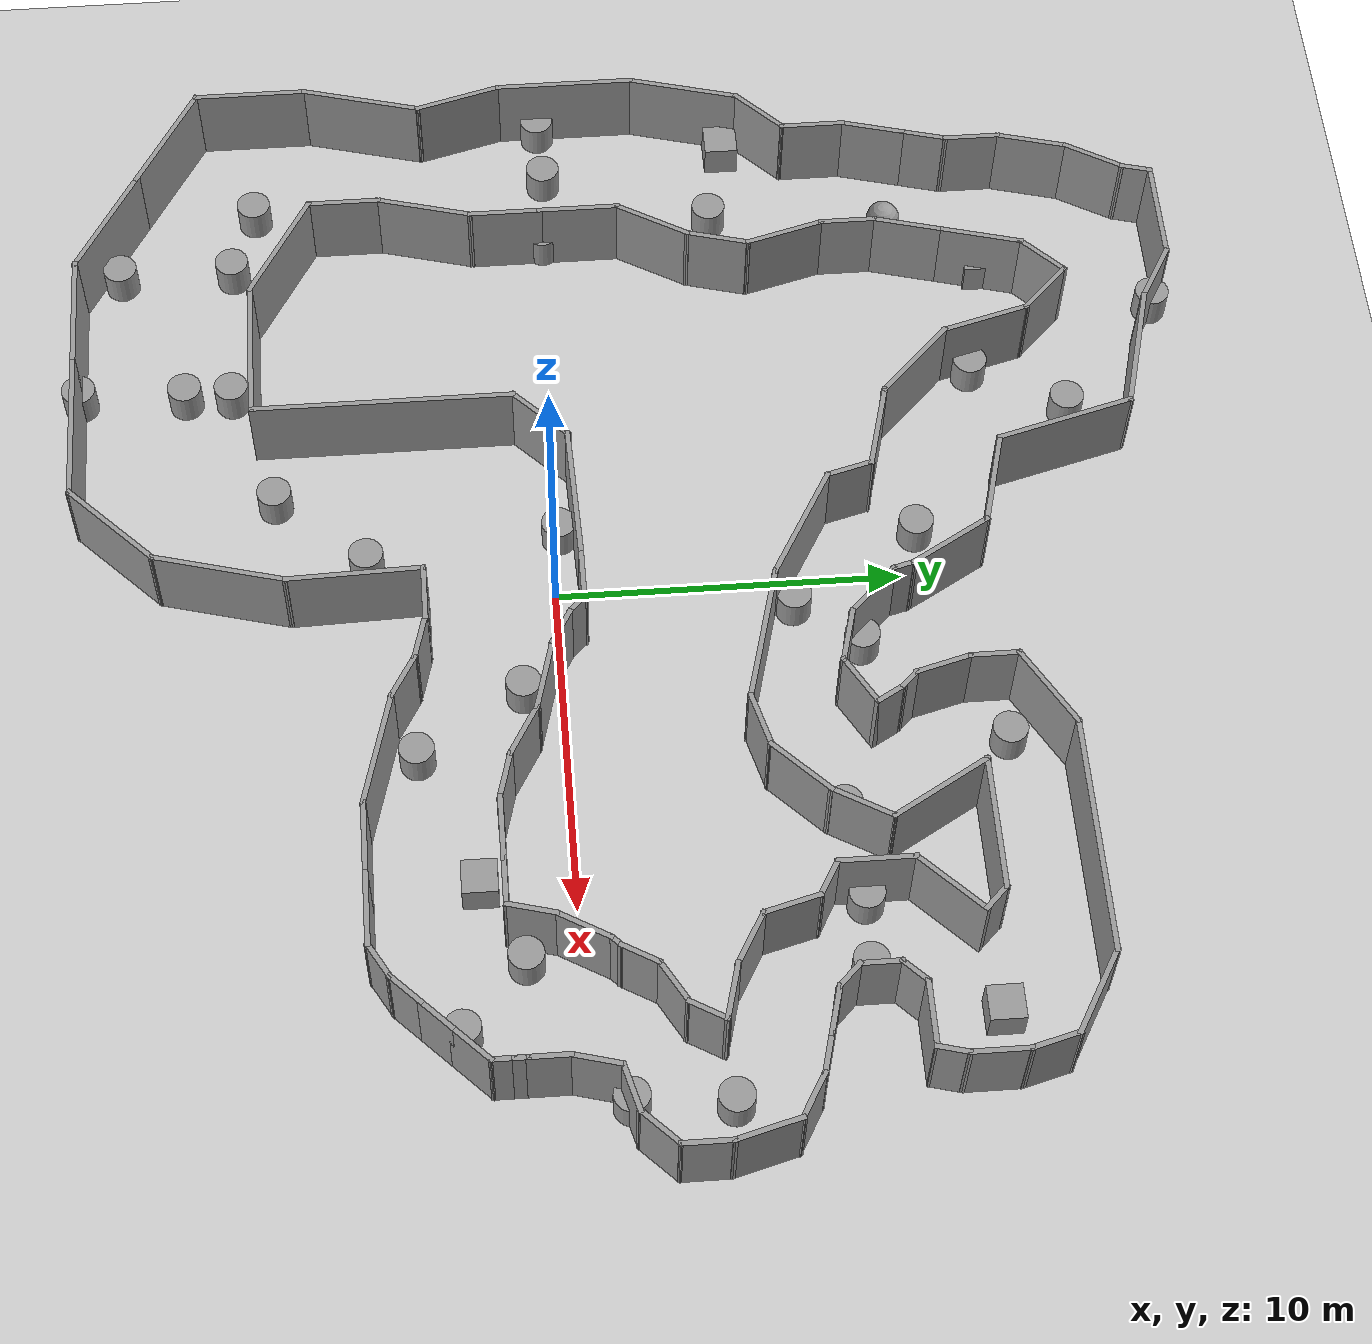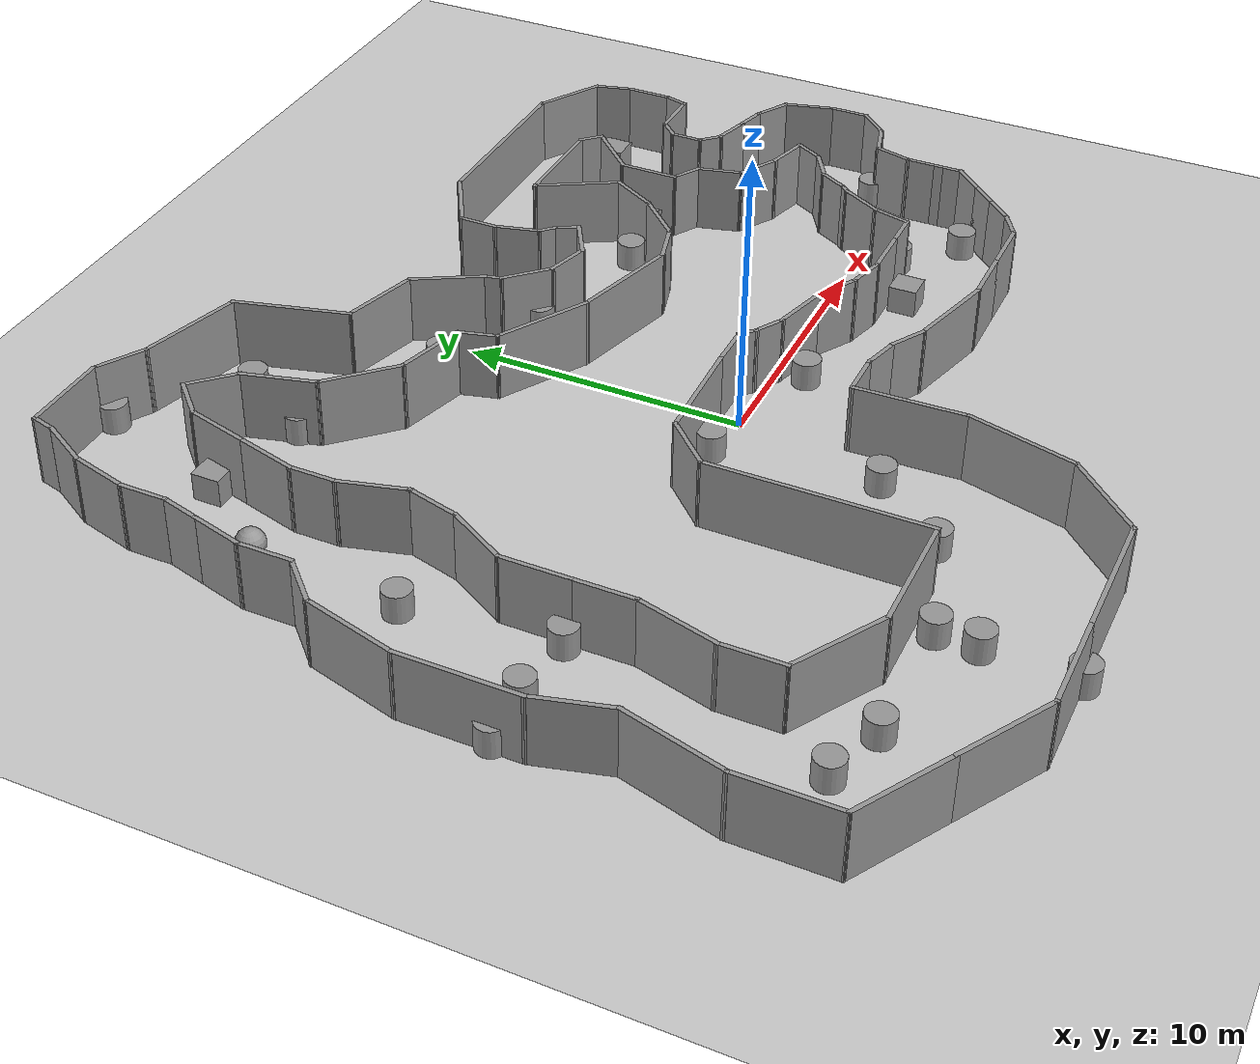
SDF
<sdf version="1.7">
 <world name="default">
  <light name="sun" type="directional">
   <pose>0 0 10 0 -0 0</pose>
   <diffuse>0.8 0.8 0.8 1</diffuse>
   <specular>0.2 0.2 0.2 1</specular>
   <attenuation>
    <range>1000</range>
    <constant>0.9</constant>
    <linear>0.01</linear>
    <quadratic>0.001</quadratic>
   </attenuation>
   <direction>-0.5 0.1 -0.9</direction>
   <spot><inner_angle>0</inner_angle><outer_angle>0</outer_angle><falloff>0</falloff></spot>
  </light>
  <model name="ground_plane">
   <static>1</static>
   <link name="link">
    <collision name="collision">
     <geometry><plane><normal>0 0 1</normal><size>100 100</size></plane></geometry>
     <surface><friction><ode><mu>100</mu><mu2>50</mu2></ode></friction></surface>
    </collision>
    <visual name="visual">
     <cast_shadows>0</cast_shadows>
     <geometry><plane><normal>0 0 1</normal><size>100 100</size></plane></geometry>
     <material>
      <script><uri>file://media/materials/scripts/gazebo.material</uri><name>Gazebo/Grey</name></script>
     </material>
    </visual>
   </link>
  </model>
  <gravity>0 0 -9.8</gravity>
  <magnetic_field>6e-06 2.3e-05 -4.2e-05</magnetic_field>
  <atmosphere type="adiabatic"/>
  <physics type="ode">
   <max_step_size>0.001</max_step_size>
   <real_time_factor>1</real_time_factor>
   <real_time_update_rate>1000</real_time_update_rate>
  </physics>
  <scene><ambient>0.4 0.4 0.4 1</ambient><background>0.7 0.7 0.7 1</background><shadows>1</shadows></scene>
  <audio><device>default</device></audio>
  <spherical_coordinates>
   <surface_model>EARTH_WGS84</surface_model>
   <latitude_deg>0</latitude_deg>
   <longitude_deg>0</longitude_deg>
   <elevation>0</elevation>
   <heading_deg>0</heading_deg>
  </spherical_coordinates>
  <model name="racetrackgap">
   <pose>0.224585 2.63558 0 0 -0 0</pose>
   <link name="Wall_10">
    <collision name="Wall_10_Collision">
     <geometry><box><size>1.25 0.15 2.5</size></box></geometry>
     <pose>0 0 1.25 0 -0 0</pose>
    </collision>
    <visual name="Wall_10_Visual">
     <pose>0 0 1.25 0 -0 0</pose>
     <geometry><box><size>1.25 0.15 2.5</size></box></geometry>
     <material>
      <script><uri>file://media/materials/scripts/gazebo.material</uri><name>Gazebo/Grey</name></script>
      <ambient>1 1 1 1</ambient>
     </material>
     <meta><layer>0</layer></meta>
    </visual>
    <pose>12.9009 -7.28003 0 0 -0 0.785398</pose>
   </link>
   <link name="Wall_100">
    <collision name="Wall_100_Collision">
     <geometry><box><size>2.75 0.15 2.5</size></box></geometry>
     <pose>0 0 1.25 0 -0 0</pose>
    </collision>
    <visual name="Wall_100_Visual">
     <pose>0 0 1.25 0 -0 0</pose>
     <geometry><box><size>2.75 0.15 2.5</size></box></geometry>
     <material>
      <script><uri>file://media/materials/scripts/gazebo.material</uri><name>Gazebo/Grey</name></script>
      <ambient>1 1 1 1</ambient>
     </material>
     <meta><layer>0</layer></meta>
    </visual>
    <pose>-3.86239 6.95839 0 0 -0 2.87979</pose>
   </link>
   <link name="Wall_101">
    <collision name="Wall_101_Collision">
     <geometry><box><size>3 0.15 2.5</size></box></geometry>
     <pose>0 0 1.25 0 -0 0</pose>
    </collision>
    <visual name="Wall_101_Visual">
     <pose>0 0 1.25 0 -0 0</pose>
     <geometry><box><size>3 0.15 2.5</size></box></geometry>
     <material>
      <script><uri>file://media/materials/scripts/gazebo.material</uri><name>Gazebo/Grey</name></script>
      <ambient>1 1 1 1</ambient>
     </material>
     <meta><layer>0</layer></meta>
    </visual>
    <pose>-6.12573 8.30248 0 0 -0 2.35619</pose>
   </link>
   <link name="Wall_102">
    <collision name="Wall_102_Collision">
     <geometry><box><size>2.75 0.15 2.5</size></box></geometry>
     <pose>0 0 1.25 0 -0 0</pose>
    </collision>
    <visual name="Wall_102_Visual">
     <pose>0 0 1.25 0 -0 0</pose>
     <geometry><box><size>2.75 0.15 2.5</size></box></geometry>
     <material>
      <script><uri>file://media/materials/scripts/gazebo.material</uri><name>Gazebo/Grey</name></script>
      <ambient>1 1 1 1</ambient>
     </material>
     <meta><layer>0</layer></meta>
    </visual>
    <pose>-7.46982 10.5658 0 0 -0 1.8326</pose>
   </link>
   <link name="Wall_103">
    <collision name="Wall_103_Collision">
     <geometry><box><size>2 0.15 2.5</size></box></geometry>
     <pose>0 0 1.25 0 -0 0</pose>
    </collision>
    <visual name="Wall_103_Visual">
     <pose>0 0 1.25 0 -0 0</pose>
     <geometry><box><size>2 0.15 2.5</size></box></geometry>
     <material>
      <script><uri>file://media/materials/scripts/gazebo.material</uri><name>Gazebo/Grey</name></script>
      <ambient>1 1 1 1</ambient>
     </material>
     <meta><layer>0</layer></meta>
    </visual>
    <pose>-8.46036 12.4756 0 0 -0 2.35619</pose>
   </link>
   <link name="Wall_104">
    <collision name="Wall_104_Collision">
     <geometry><box><size>1.75 0.15 2.5</size></box></geometry>
     <pose>0 0 1.25 0 -0 0</pose>
    </collision>
    <visual name="Wall_104_Visual">
     <pose>0 0 1.25 0 -0 0</pose>
     <geometry><box><size>1.75 0.15 2.5</size></box></geometry>
     <material>
      <script><uri>file://media/materials/scripts/gazebo.material</uri><name>Gazebo/Grey</name></script>
      <ambient>1 1 1 1</ambient>
     </material>
     <meta><layer>0</layer></meta>
    </visual>
    <pose>-9.68012 12.564 0 0 -0 -2.35619</pose>
   </link>
   <link name="Wall_105">
    <collision name="Wall_105_Collision">
     <geometry><box><size>2.5 0.15 2.5</size></box></geometry>
     <pose>0 0 1.25 0 -0 0</pose>
    </collision>
    <visual name="Wall_105_Visual">
     <pose>0 0 1.25 0 -0 0</pose>
     <geometry><box><size>2.5 0.15 2.5</size></box></geometry>
     <material>
      <script><uri>file://media/materials/scripts/gazebo.material</uri><name>Gazebo/Grey</name></script>
      <ambient>1 1 1 1</ambient>
     </material>
     <meta><layer>0</layer></meta>
    </visual>
    <pose>-10.5499 10.8633 0 0 -0 -1.8326</pose>
   </link>
   <link name="Wall_106">
    <collision name="Wall_106_Collision">
     <geometry><box><size>2.25 0.15 2.5</size></box></geometry>
     <pose>0 0 1.25 0 -0 0</pose>
    </collision>
    <visual name="Wall_106_Visual">
     <pose>0 0 1.25 0 -0 0</pose>
     <geometry><box><size>2.25 0.15 2.5</size></box></geometry>
     <material>
      <script><uri>file://media/materials/scripts/gazebo.material</uri><name>Gazebo/Grey</name></script>
      <ambient>1 1 1 1</ambient>
     </material>
     <meta><layer>0</layer></meta>
    </visual>
    <pose>-11.1258 8.71414 0 0 -0 -1.8326</pose>
   </link>
   <link name="Wall_107">
    <collision name="Wall_107_Collision">
     <geometry><box><size>1.75 0.15 2.5</size></box></geometry>
     <pose>0 0 1.25 0 -0 0</pose>
    </collision>
    <visual name="Wall_107_Visual">
     <pose>0 0 1.25 0 -0 0</pose>
     <geometry><box><size>1.75 0.15 2.5</size></box></geometry>
     <material>
      <script><uri>file://media/materials/scripts/gazebo.material</uri><name>Gazebo/Grey</name></script>
      <ambient>1 1 1 1</ambient>
     </material>
     <meta><layer>0</layer></meta>
    </visual>
    <pose>-11.3975 6.89992 0 0 -0 -1.5708</pose>
   </link>
   <link name="Wall_108">
    <collision name="Wall_108_Collision">
     <geometry><box><size>2.5 0.15 2.5</size></box></geometry>
     <pose>0 0 1.25 0 -0 0</pose>
    </collision>
    <visual name="Wall_108_Visual">
     <pose>0 0 1.25 0 -0 0</pose>
     <geometry><box><size>2.5 0.15 2.5</size></box></geometry>
     <material>
      <script><uri>file://media/materials/scripts/gazebo.material</uri><name>Gazebo/Grey</name></script>
      <ambient>1 1 1 1</ambient>
     </material>
     <meta><layer>0</layer></meta>
    </visual>
    <pose>-11.0934 4.96496 0 0 -0 -1.309</pose>
   </link>
   <link name="Wall_109">
    <collision name="Wall_109_Collision">
     <geometry><box><size>2 0.15 2.5</size></box></geometry>
     <pose>0 0 1.25 0 -0 0</pose>
    </collision>
    <visual name="Wall_109_Visual">
     <pose>0 0 1.25 0 -0 0</pose>
     <geometry><box><size>2 0.15 2.5</size></box></geometry>
     <material>
      <script><uri>file://media/materials/scripts/gazebo.material</uri><name>Gazebo/Grey</name></script>
      <ambient>1 1 1 1</ambient>
     </material>
     <meta><layer>0</layer></meta>
    </visual>
    <pose>-11.0287 2.93651 0 0 -0 -1.8326</pose>
   </link>
   <link name="Wall_11">
    <collision name="Wall_11_Collision">
     <geometry><box><size>1.25 0.15 2.5</size></box></geometry>
     <pose>0 0 1.25 0 -0 0</pose>
    </collision>
    <visual name="Wall_11_Visual">
     <pose>0 0 1.25 0 -0 0</pose>
     <geometry><box><size>1.25 0.15 2.5</size></box></geometry>
     <material>
      <script><uri>file://media/materials/scripts/gazebo.material</uri><name>Gazebo/Grey</name></script>
      <ambient>1 1 1 1</ambient>
     </material>
     <meta><layer>0</layer></meta>
    </visual>
    <pose>13.6788 -6.50221 0 0 -0 0.785398</pose>
   </link>
   <link name="Wall_110">
    <collision name="Wall_110_Collision">
     <geometry><box><size>2.5 0.15 2.5</size></box></geometry>
     <pose>0 0 1.25 0 -0 0</pose>
    </collision>
    <visual name="Wall_110_Visual">
     <pose>0 0 1.25 0 -0 0</pose>
     <geometry><box><size>2.5 0.15 2.5</size></box></geometry>
     <material>
      <script><uri>file://media/materials/scripts/gazebo.material</uri><name>Gazebo/Grey</name></script>
      <ambient>1 1 1 1</ambient>
     </material>
     <meta><layer>0</layer></meta>
    </visual>
    <pose>-11.8556 1.02545 0 0 -0 -2.0944</pose>
   </link>
   <link name="Wall_111">
    <collision name="Wall_111_Collision">
     <geometry><box><size>2.5 0.15 2.5</size></box></geometry>
     <pose>0 0 1.25 0 -0 0</pose>
    </collision>
    <visual name="Wall_111_Visual">
     <pose>0 0 1.25 0 -0 0</pose>
     <geometry><box><size>2.5 0.15 2.5</size></box></geometry>
     <material>
      <script><uri>file://media/materials/scripts/gazebo.material</uri><name>Gazebo/Grey</name></script>
      <ambient>1 1 1 1</ambient>
     </material>
     <meta><layer>0</layer></meta>
    </visual>
    <pose>-12.4431 -1.16713 0 0 -0 -1.5708</pose>
   </link>
   <link name="Wall_112">
    <collision name="Wall_112_Collision">
     <geometry><box><size>2.25 0.15 2.5</size></box></geometry>
     <pose>0 0 1.25 0 -0 0</pose>
    </collision>
    <visual name="Wall_112_Visual">
     <pose>0 0 1.25 0 -0 0</pose>
     <geometry><box><size>2.25 0.15 2.5</size></box></geometry>
     <material>
      <script><uri>file://media/materials/scripts/gazebo.material</uri><name>Gazebo/Grey</name></script>
      <ambient>1 1 1 1</ambient>
     </material>
     <meta><layer>0</layer></meta>
    </visual>
    <pose>-12.4431 -3.39213 0 0 -0 -1.5708</pose>
   </link>
   <link name="Wall_113">
    <collision name="Wall_113_Collision">
     <geometry><box><size>3 0.15 2.5</size></box></geometry>
     <pose>0 0 1.25 0 -0 0</pose>
    </collision>
    <visual name="Wall_113_Visual">
     <pose>0 0 1.25 0 -0 0</pose>
     <geometry><box><size>3 0.15 2.5</size></box></geometry>
     <material>
      <script><uri>file://media/materials/scripts/gazebo.material</uri><name>Gazebo/Grey</name></script>
      <ambient>1 1 1 1</ambient>
     </material>
     <meta><layer>0</layer></meta>
    </visual>
    <pose>-12.812 -5.81857 0 0 -0 -1.8326</pose>
   </link>
   <link name="Wall_114">
    <collision name="Wall_114_Collision">
     <geometry><box><size>2.25 0.15 2.5</size></box></geometry>
     <pose>0 0 1.25 0 -0 0</pose>
    </collision>
    <visual name="Wall_114_Visual">
     <pose>0 0 1.25 0 -0 0</pose>
     <geometry><box><size>2.25 0.15 2.5</size></box></geometry>
     <material>
      <script><uri>file://media/materials/scripts/gazebo.material</uri><name>Gazebo/Grey</name></script>
      <ambient>1 1 1 1</ambient>
     </material>
     <meta><layer>0</layer></meta>
    </visual>
    <pose>-13.1808 -8.24502 0 0 -0 -1.5708</pose>
   </link>
   <link name="Wall_115">
    <collision name="Wall_115_Collision">
     <geometry><box><size>3.75 0.15 2.5</size></box></geometry>
     <pose>0 0 1.25 0 -0 0</pose>
    </collision>
    <visual name="Wall_115_Visual">
     <pose>0 0 1.25 0 -0 0</pose>
     <geometry><box><size>3.75 0.15 2.5</size></box></geometry>
     <material>
      <script><uri>file://media/materials/scripts/gazebo.material</uri><name>Gazebo/Grey</name></script>
      <ambient>1 1 1 1</ambient>
     </material>
     <meta><layer>0</layer></meta>
    </visual>
    <pose>-11.6219 -10.195 0 0 -0 -0.523599</pose>
   </link>
   <link name="Wall_116">
    <collision name="Wall_116_Collision">
     <geometry><box><size>4.5 0.15 2.5</size></box></geometry>
     <pose>0 0 1.25 0 -0 0</pose>
    </collision>
    <visual name="Wall_116_Visual">
     <pose>0 0 1.25 0 -0 0</pose>
     <geometry><box><size>4.5 0.15 2.5</size></box></geometry>
     <material>
      <script><uri>file://media/materials/scripts/gazebo.material</uri><name>Gazebo/Grey</name></script>
      <ambient>1 1 1 1</ambient>
     </material>
     <meta><layer>0</layer></meta>
    </visual>
    <pose>-7.88808 -11.095 0 0 -0 0</pose>
   </link>
   <link name="Wall_117">
    <collision name="Wall_117_Collision">
     <geometry><box><size>7.75 0.15 2.5</size></box></geometry>
     <pose>0 0 1.25 0 -0 0</pose>
    </collision>
    <visual name="Wall_117_Visual">
     <pose>0 0 1.25 0 -0 0</pose>
     <geometry><box><size>7.75 0.15 2.5</size></box></geometry>
     <material>
      <script><uri>file://media/materials/scripts/gazebo.material</uri><name>Gazebo/Grey</name></script>
      <ambient>1 1 1 1</ambient>
     </material>
     <meta><layer>0</layer></meta>
    </visual>
    <pose>-5.71308 -7.29502 0 0 -0 1.5708</pose>
   </link>
   <link name="Wall_118">
    <collision name="Wall_118_Collision">
     <geometry><box><size>2.25 0.15 2.5</size></box></geometry>
     <pose>0 0 1.25 0 -0 0</pose>
    </collision>
    <visual name="Wall_118_Visual">
     <pose>0 0 1.25 0 -0 0</pose>
     <geometry><box><size>2.25 0.15 2.5</size></box></geometry>
     <material>
      <script><uri>file://media/materials/scripts/gazebo.material</uri><name>Gazebo/Grey</name></script>
      <ambient>1 1 1 1</ambient>
     </material>
     <meta><layer>0</layer></meta>
    </visual>
    <pose>-4.97062 -2.75255 0 0 -0 0.785398</pose>
   </link>
   <link name="Wall_119">
    <collision name="Wall_119_Collision">
     <geometry><box><size>4.13259 0.15 2.5</size></box></geometry>
     <pose>0 0 1.25 0 -0 0</pose>
    </collision>
    <visual name="Wall_119_Visual">
     <pose>0 0 1.25 0 -0 0</pose>
     <geometry><box><size>4.13259 0.15 2.5</size></box></geometry>
     <material>
      <script><uri>file://media/materials/scripts/gazebo.material</uri><name>Gazebo/Grey</name></script>
      <ambient>1 1 1 1</ambient>
     </material>
     <meta><layer>0</layer></meta>
    </visual>
    <pose>-2.23793 -1.945 0 0 -0 0.032696</pose>
   </link>
   <link name="Wall_12">
    <collision name="Wall_12_Collision">
     <geometry><box><size>1.5 0.15 2.5</size></box></geometry>
     <pose>0 0 1.25 0 -0 0</pose>
    </collision>
    <visual name="Wall_12_Visual">
     <pose>0 0 1.25 0 -0 0</pose>
     <geometry><box><size>1.5 0.15 2.5</size></box></geometry>
     <material>
      <script><uri>file://media/materials/scripts/gazebo.material</uri><name>Gazebo/Grey</name></script>
      <ambient>1 1 1 1</ambient>
     </material>
     <meta><layer>0</layer></meta>
    </visual>
    <pose>14.545 -5.63601 0 0 -0 0.785398</pose>
   </link>
   <link name="Wall_13">
    <collision name="Wall_13_Collision">
     <geometry><box><size>0.75 0.15 2.5</size></box></geometry>
     <pose>0 0 1.25 0 -0 0</pose>
    </collision>
    <visual name="Wall_13_Visual">
     <pose>0 0 1.25 0 -0 0</pose>
     <geometry><box><size>0.75 0.15 2.5</size></box></geometry>
     <material>
      <script><uri>file://media/materials/scripts/gazebo.material</uri><name>Gazebo/Grey</name></script>
      <ambient>1 1 1 1</ambient>
     </material>
     <meta><layer>0</layer></meta>
    </visual>
    <pose>15.0223 -4.85871 0 0 -0 1.5708</pose>
   </link>
   <link name="Wall_14">
    <collision name="Wall_14_Collision">
     <geometry><box><size>0.5 0.15 2.5</size></box></geometry>
     <pose>0 0 1.25 0 -0 0</pose>
    </collision>
    <visual name="Wall_14_Visual">
     <pose>0 0 1.25 0 -0 0</pose>
     <geometry><box><size>0.5 0.15 2.5</size></box></geometry>
     <material>
      <script><uri>file://media/materials/scripts/gazebo.material</uri><name>Gazebo/Grey</name></script>
      <ambient>1 1 1 1</ambient>
     </material>
     <meta><layer>0</layer></meta>
    </visual>
    <pose>15.0223 -4.38371 0 0 -0 1.5708</pose>
   </link>
   <link name="Wall_15">
    <collision name="Wall_15_Collision">
     <geometry><box><size>1.25 0.15 2.5</size></box></geometry>
     <pose>0 0 1.25 0 -0 0</pose>
    </collision>
    <visual name="Wall_15_Visual">
     <pose>0 0 1.25 0 -0 0</pose>
     <geometry><box><size>1.25 0.15 2.5</size></box></geometry>
     <material>
      <script><uri>file://media/materials/scripts/gazebo.material</uri><name>Gazebo/Grey</name></script>
      <ambient>1 1 1 1</ambient>
     </material>
     <meta><layer>0</layer></meta>
    </visual>
    <pose>15.0223 -3.65871 0 0 -0 1.5708</pose>
   </link>
   <link name="Wall_16">
    <collision name="Wall_16_Collision">
     <geometry><box><size>1.5 0.15 2.5</size></box></geometry>
     <pose>0 0 1.25 0 -0 0</pose>
    </collision>
    <visual name="Wall_16_Visual">
     <pose>0 0 1.25 0 -0 0</pose>
     <geometry><box><size>1.5 0.15 2.5</size></box></geometry>
     <material>
      <script><uri>file://media/materials/scripts/gazebo.material</uri><name>Gazebo/Grey</name></script>
      <ambient>1 1 1 1</ambient>
     </material>
     <meta><layer>0</layer></meta>
    </visual>
    <pose>15.197 -2.45671 0 0 -0 1.309</pose>
   </link>
   <link name="Wall_17">
    <collision name="Wall_17_Collision">
     <geometry><box><size>1.5 0.15 2.5</size></box></geometry>
     <pose>0 0 1.25 0 -0 0</pose>
    </collision>
    <visual name="Wall_17_Visual">
     <pose>0 0 1.25 0 -0 0</pose>
     <geometry><box><size>1.5 0.15 2.5</size></box></geometry>
     <material>
      <script><uri>file://media/materials/scripts/gazebo.material</uri><name>Gazebo/Grey</name></script>
      <ambient>1 1 1 1</ambient>
     </material>
     <meta><layer>0</layer></meta>
    </visual>
    <pose>16.0237 -1.63001 0 0 -0 0.261799</pose>
   </link>
   <link name="Wall_18">
    <collision name="Wall_18_Collision">
     <geometry><box><size>1.5 0.15 2.5</size></box></geometry>
     <pose>0 0 1.25 0 -0 0</pose>
    </collision>
    <visual name="Wall_18_Visual">
     <pose>0 0 1.25 0 -0 0</pose>
     <geometry><box><size>1.5 0.15 2.5</size></box></geometry>
     <material>
      <script><uri>file://media/materials/scripts/gazebo.material</uri><name>Gazebo/Grey</name></script>
      <ambient>1 1 1 1</ambient>
     </material>
     <meta><layer>0</layer></meta>
    </visual>
    <pose>17.153 -0.978009 0 0 -0 0.785398</pose>
   </link>
   <link name="Wall_19">
    <collision name="Wall_19_Collision">
     <geometry><box><size>1.5 0.15 2.5</size></box></geometry>
     <pose>0 0 1.25 0 -0 0</pose>
    </collision>
    <visual name="Wall_19_Visual">
     <pose>0 0 1.25 0 -0 0</pose>
     <geometry><box><size>1.5 0.15 2.5</size></box></geometry>
     <material>
      <script><uri>file://media/materials/scripts/gazebo.material</uri><name>Gazebo/Grey</name></script>
      <ambient>1 1 1 1</ambient>
     </material>
     <meta><layer>0</layer></meta>
    </visual>
    <pose>17.6303 0.174289 0 0 -0 1.5708</pose>
   </link>
   <link name="Wall_20">
    <collision name="Wall_20_Collision">
     <geometry><box><size>2 0.15 2.5</size></box></geometry>
     <pose>0 0 1.25 0 -0 0</pose>
    </collision>
    <visual name="Wall_20_Visual">
     <pose>0 0 1.25 0 -0 0</pose>
     <geometry><box><size>2 0.15 2.5</size></box></geometry>
     <material>
      <script><uri>file://media/materials/scripts/gazebo.material</uri><name>Gazebo/Grey</name></script>
      <ambient>1 1 1 1</ambient>
     </material>
     <meta><layer>0</layer></meta>
    </visual>
    <pose>17.3909 1.74277 0 0 -0 1.8326</pose>
   </link>
   <link name="Wall_21">
    <collision name="Wall_21_Collision">
     <geometry><box><size>1.5 0.15 2.5</size></box></geometry>
     <pose>0 0 1.25 0 -0 0</pose>
    </collision>
    <visual name="Wall_21_Visual">
     <pose>0 0 1.25 0 -0 0</pose>
     <geometry><box><size>1.5 0.15 2.5</size></box></geometry>
     <material>
      <script><uri>file://media/materials/scripts/gazebo.material</uri><name>Gazebo/Grey</name></script>
      <ambient>1 1 1 1</ambient>
     </material>
     <meta><layer>0</layer></meta>
    </visual>
    <pose>16.5669 2.97375 0 0 -0 2.61799</pose>
   </link>
   <link name="Wall_22">
    <collision name="Wall_22_Collision">
     <geometry><box><size>1.25 0.15 2.5</size></box></geometry>
     <pose>0 0 1.25 0 -0 0</pose>
    </collision>
    <visual name="Wall_22_Visual">
     <pose>0 0 1.25 0 -0 0</pose>
     <geometry><box><size>1.25 0.15 2.5</size></box></geometry>
     <material>
      <script><uri>file://media/materials/scripts/gazebo.material</uri><name>Gazebo/Grey</name></script>
      <ambient>1 1 1 1</ambient>
     </material>
     <meta><layer>0</layer></meta>
    </visual>
    <pose>15.4511 3.4536 0 0 -0 2.87979</pose>
   </link>
   <link name="Wall_23">
    <collision name="Wall_23_Collision">
     <geometry><box><size>1.5 0.15 2.5</size></box></geometry>
     <pose>0 0 1.25 0 -0 0</pose>
    </collision>
    <visual name="Wall_23_Visual">
     <pose>0 0 1.25 0 -0 0</pose>
     <geometry><box><size>1.5 0.15 2.5</size></box></geometry>
     <material>
      <script><uri>file://media/materials/scripts/gazebo.material</uri><name>Gazebo/Grey</name></script>
      <ambient>1 1 1 1</ambient>
     </material>
     <meta><layer>0</layer></meta>
    </visual>
    <pose>14.2678 3.77066 0 0 -0 2.87979</pose>
   </link>
   <link name="Wall_24">
    <collision name="Wall_24_Collision">
     <geometry><box><size>1 0.15 2.5</size></box></geometry>
     <pose>0 0 1.25 0 -0 0</pose>
    </collision>
    <visual name="Wall_24_Visual">
     <pose>0 0 1.25 0 -0 0</pose>
     <geometry><box><size>1 0.15 2.5</size></box></geometry>
     <material>
      <script><uri>file://media/materials/scripts/gazebo.material</uri><name>Gazebo/Grey</name></script>
      <ambient>1 1 1 1</ambient>
     </material>
     <meta><layer>0</layer></meta>
    </visual>
    <pose>13.3153 4.24588 0 0 -0 2.35619</pose>
   </link>
   <link name="Wall_27">
    <collision name="Wall_27_Collision">
     <geometry><box><size>1.25 0.15 2.5</size></box></geometry>
     <pose>0 0 1.25 0 -0 0</pose>
    </collision>
    <visual name="Wall_27_Visual">
     <pose>0 0 1.25 0 -0 0</pose>
     <geometry><box><size>1.25 0.15 2.5</size></box></geometry>
     <material>
      <script><uri>file://media/materials/scripts/gazebo.material</uri><name>Gazebo/Grey</name></script>
      <ambient>1 1 1 1</ambient>
     </material>
     <meta><layer>0</layer></meta>
    </visual>
    <pose>13.0148 5.0964 0 0 -0 1.5708</pose>
   </link>
   <link name="Wall_28">
    <collision name="Wall_28_Collision">
     <geometry><box><size>1 0.15 2.5</size></box></geometry>
     <pose>0 0 1.25 0 -0 0</pose>
    </collision>
    <visual name="Wall_28_Visual">
     <pose>0 0 1.25 0 -0 0</pose>
     <geometry><box><size>1 0.15 2.5</size></box></geometry>
     <material>
      <script><uri>file://media/materials/scripts/gazebo.material</uri><name>Gazebo/Grey</name></script>
      <ambient>1 1 1 1</ambient>
     </material>
     <meta><layer>0</layer></meta>
    </visual>
    <pose>13.3153 5.94692 0 0 -0 0.785398</pose>
   </link>
   <link name="Wall_29">
    <collision name="Wall_29_Collision">
     <geometry><box><size>2 0.15 2.5</size></box></geometry>
     <pose>0 0 1.25 0 -0 0</pose>
    </collision>
    <visual name="Wall_29_Visual">
     <pose>0 0 1.25 0 -0 0</pose>
     <geometry><box><size>2 0.15 2.5</size></box></geometry>
     <material>
      <script><uri>file://media/materials/scripts/gazebo.material</uri><name>Gazebo/Grey</name></script>
      <ambient>1 1 1 1</ambient>
     </material>
     <meta><layer>0</layer></meta>
    </visual>
    <pose>14.5408 6.24744 0 0 -0 0</pose>
   </link>
   <link name="Wall_3">
    <collision name="Wall_3_Collision">
     <geometry><box><size>1.75 0.15 2.5</size></box></geometry>
     <pose>0 0 1.25 0 -0 0</pose>
    </collision>
    <visual name="Wall_3_Visual">
     <pose>0 0 1.25 0 -0 0</pose>
     <geometry><box><size>1.75 0.15 2.5</size></box></geometry>
     <material>
      <script><uri>file://media/materials/scripts/gazebo.material</uri><name>Gazebo/Grey</name></script>
      <ambient>1 1 1 1</ambient>
     </material>
     <meta><layer>0</layer></meta>
    </visual>
    <pose>0.850427 -6.32749 0 0 -0 0</pose>
   </link>
   <link name="Wall_30">
    <collision name="Wall_30_Collision">
     <geometry><box><size>1 0.15 2.5</size></box></geometry>
     <pose>0 0 1.25 0 -0 0</pose>
    </collision>
    <visual name="Wall_30_Visual">
     <pose>0 0 1.25 0 -0 0</pose>
     <geometry><box><size>1 0.15 2.5</size></box></geometry>
     <material>
      <script><uri>file://media/materials/scripts/gazebo.material</uri><name>Gazebo/Grey</name></script>
      <ambient>1 1 1 1</ambient>
     </material>
     <meta><layer>0</layer></meta>
    </visual>
    <pose>15.5758 6.65796 0 0 -0 1.309</pose>
   </link>
   <link name="Wall_31">
    <collision name="Wall_31_Collision">
     <geometry><box><size>1.75 0.15 2.5</size></box></geometry>
     <pose>0 0 1.25 0 -0 0</pose>
    </collision>
    <visual name="Wall_31_Visual">
     <pose>0 0 1.25 0 -0 0</pose>
     <geometry><box><size>1.75 0.15 2.5</size></box></geometry>
     <material>
      <script><uri>file://media/materials/scripts/gazebo.material</uri><name>Gazebo/Grey</name></script>
      <ambient>1 1 1 1</ambient>
     </material>
     <meta><layer>0</layer></meta>
    </visual>
    <pose>15.6858 7.86848 0 0 -0 1.5708</pose>
   </link>
   <link name="Wall_32">
    <collision name="Wall_32_Collision">
     <geometry><box><size>1.5 0.15 2.5</size></box></geometry>
     <pose>0 0 1.25 0 -0 0</pose>
    </collision>
    <visual name="Wall_32_Visual">
     <pose>0 0 1.25 0 -0 0</pose>
     <geometry><box><size>1.5 0.15 2.5</size></box></geometry>
     <material>
      <script><uri>file://media/materials/scripts/gazebo.material</uri><name>Gazebo/Grey</name></script>
      <ambient>1 1 1 1</ambient>
     </material>
     <meta><layer>0</layer></meta>
    </visual>
    <pose>15.5111 9.32048 0 0 -0 1.8326</pose>
   </link>
   <link name="Wall_33">
    <collision name="Wall_33_Collision">
     <geometry><box><size>2.75 0.15 2.5</size></box></geometry>
     <pose>0 0 1.25 0 -0 0</pose>
    </collision>
    <visual name="Wall_33_Visual">
     <pose>0 0 1.25 0 -0 0</pose>
     <geometry><box><size>2.75 0.15 2.5</size></box></geometry>
     <material>
      <script><uri>file://media/materials/scripts/gazebo.material</uri><name>Gazebo/Grey</name></script>
      <ambient>1 1 1 1</ambient>
     </material>
     <meta><layer>0</layer></meta>
    </visual>
    <pose>14.2106 10.6225 0 0 -0 2.61799</pose>
   </link>
   <link name="Wall_34">
    <collision name="Wall_34_Collision">
     <geometry><box><size>7 0.15 2.5</size></box></geometry>
     <pose>0 0 1.25 0 -0 0</pose>
    </collision>
    <visual name="Wall_34_Visual">
     <pose>0 0 1.25 0 -0 0</pose>
     <geometry><box><size>7 0.15 2.5</size></box></geometry>
     <material>
      <script><uri>file://media/materials/scripts/gazebo.material</uri><name>Gazebo/Grey</name></script>
      <ambient>1 1 1 1</ambient>
     </material>
     <meta><layer>0</layer></meta>
    </visual>
    <pose>9.65973 11.2725 0 0 -0 3.14159</pose>
   </link>
   <link name="Wall_35">
    <collision name="Wall_35_Collision">
     <geometry><box><size>2.75 0.15 2.5</size></box></geometry>
     <pose>0 0 1.25 0 -0 0</pose>
    </collision>
    <visual name="Wall_35_Visual">
     <pose>0 0 1.25 0 -0 0</pose>
     <geometry><box><size>2.75 0.15 2.5</size></box></geometry>
     <material>
      <script><uri>file://media/materials/scripts/gazebo.material</uri><name>Gazebo/Grey</name></script>
      <ambient>1 1 1 1</ambient>
     </material>
     <meta><layer>0</layer></meta>
    </visual>
    <pose>5.10889 10.6225 0 0 -0 -2.61799</pose>
   </link>
   <link name="Wall_36">
    <collision name="Wall_36_Collision">
     <geometry><box><size>1.5 0.15 2.5</size></box></geometry>
     <pose>0 0 1.25 0 -0 0</pose>
    </collision>
    <visual name="Wall_36_Visual">
     <pose>0 0 1.25 0 -0 0</pose>
     <geometry><box><size>1.5 0.15 2.5</size></box></geometry>
     <material>
      <script><uri>file://media/materials/scripts/gazebo.material</uri><name>Gazebo/Grey</name></script>
      <ambient>1 1 1 1</ambient>
     </material>
     <meta><layer>0</layer></meta>
    </visual>
    <pose>3.98306 9.29748 0 0 -0 -1.5708</pose>
   </link>
   <link name="Wall_37">
    <collision name="Wall_37_Collision">
     <geometry><box><size>1.75 0.15 2.5</size></box></geometry>
     <pose>0 0 1.25 0 -0 0</pose>
    </collision>
    <visual name="Wall_37_Visual">
     <pose>0 0 1.25 0 -0 0</pose>
     <geometry><box><size>1.75 0.15 2.5</size></box></geometry>
     <material>
      <script><uri>file://media/materials/scripts/gazebo.material</uri><name>Gazebo/Grey</name></script>
      <ambient>1 1 1 1</ambient>
     </material>
     <meta><layer>0</layer></meta>
    </visual>
    <pose>4.19011 7.84974 0 0 -0 -1.309</pose>
   </link>
   <link name="Wall_38">
    <collision name="Wall_38_Collision">
     <geometry><box><size>0.75 0.15 2.5</size></box></geometry>
     <pose>0 0 1.25 0 -0 0</pose>
    </collision>
    <visual name="Wall_38_Visual">
     <pose>0 0 1.25 0 -0 0</pose>
     <geometry><box><size>0.75 0.15 2.5</size></box></geometry>
     <material>
      <script><uri>file://media/materials/scripts/gazebo.material</uri><name>Gazebo/Grey</name></script>
      <ambient>1 1 1 1</ambient>
     </material>
     <meta><layer>0</layer></meta>
    </visual>
    <pose>4.6093 6.86486 0 0 -0 -0.785398</pose>
   </link>
   <link name="Wall_39">
    <collision name="Wall_39_Collision">
     <geometry><box><size>1 0.15 2.5</size></box></geometry>
     <pose>0 0 1.25 0 -0 0</pose>
    </collision>
    <visual name="Wall_39_Visual">
     <pose>0 0 1.25 0 -0 0</pose>
     <geometry><box><size>1 0.15 2.5</size></box></geometry>
     <material>
      <script><uri>file://media/materials/scripts/gazebo.material</uri><name>Gazebo/Grey</name></script>
      <ambient>1 1 1 1</ambient>
     </material>
     <meta><layer>0</layer></meta>
    </visual>
    <pose>5.03393 6.28467 0 0 -0 -1.0472</pose>
   </link>
   <link name="Wall_4">
    <collision name="Wall_4_Collision">
     <geometry><box><size>1.5 0.15 2.5</size></box></geometry>
     <pose>0 0 1.25 0 -0 0</pose>
    </collision>
    <visual name="Wall_4_Visual">
     <pose>0 0 1.25 0 -0 0</pose>
     <geometry><box><size>1.5 0.15 2.5</size></box></geometry>
     <material>
      <script><uri>file://media/materials/scripts/gazebo.material</uri><name>Gazebo/Grey</name></script>
      <ambient>1 1 1 1</ambient>
     </material>
     <meta><layer>0</layer></meta>
    </visual>
    <pose>2.30243 -6.50219 0 0 -0 -0.261799</pose>
   </link>
   <link name="Wall_40">
    <collision name="Wall_40_Collision">
     <geometry><box><size>1.75 0.15 2.5</size></box></geometry>
     <pose>0 0 1.25 0 -0 0</pose>
    </collision>
    <visual name="Wall_40_Visual">
     <pose>0 0 1.25 0 -0 0</pose>
     <geometry><box><size>1.75 0.15 2.5</size></box></geometry>
     <material>
      <script><uri>file://media/materials/scripts/gazebo.material</uri><name>Gazebo/Grey</name></script>
      <ambient>1 1 1 1</ambient>
     </material>
     <meta><layer>0</layer></meta>
    </visual>
    <pose>4.55361 5.51661 0 0 -0 -2.61799</pose>
   </link>
   <link name="Wall_41">
    <collision name="Wall_41_Collision">
     <geometry><box><size>1.75 0.15 2.5</size></box></geometry>
     <pose>0 0 1.25 0 -0 0</pose>
    </collision>
    <visual name="Wall_41_Visual">
     <pose>0 0 1.25 0 -0 0</pose>
     <geometry><box><size>1.75 0.15 2.5</size></box></geometry>
     <material>
      <script><uri>file://media/materials/scripts/gazebo.material</uri><name>Gazebo/Grey</name></script>
      <ambient>1 1 1 1</ambient>
     </material>
     <meta><layer>0</layer></meta>
    </visual>
    <pose>3.08805 5.32367 0 0 -0 2.87979</pose>
   </link>
   <link name="Wall_42">
    <collision name="Wall_42_Collision">
     <geometry><box><size>2 0.15 2.5</size></box></geometry>
     <pose>0 0 1.25 0 -0 0</pose>
    </collision>
    <visual name="Wall_42_Visual">
     <pose>0 0 1.25 0 -0 0</pose>
     <geometry><box><size>2 0.15 2.5</size></box></geometry>
     <material>
      <script><uri>file://media/materials/scripts/gazebo.material</uri><name>Gazebo/Grey</name></script>
      <ambient>1 1 1 1</ambient>
     </material>
     <meta><layer>0</layer></meta>
    </visual>
    <pose>1.66124 6.18479 0 0 -0 2.35619</pose>
   </link>
   <link name="Wall_43">
    <collision name="Wall_43_Collision">
     <geometry><box><size>0.75 0.15 2.5</size></box></geometry>
     <pose>0 0 1.25 0 -0 0</pose>
    </collision>
    <visual name="Wall_43_Visual">
     <pose>0 0 1.25 0 -0 0</pose>
     <geometry><box><size>0.75 0.15 2.5</size></box></geometry>
     <material>
      <script><uri>file://media/materials/scripts/gazebo.material</uri><name>Gazebo/Grey</name></script>
      <ambient>1 1 1 1</ambient>
     </material>
     <meta><layer>0</layer></meta>
    </visual>
    <pose>0.929519 7.12864 0 0 -0 1.8326</pose>
   </link>
   <link name="Wall_44">
    <collision name="Wall_44_Collision">
     <geometry><box><size>2.75 0.15 2.5</size></box></geometry>
     <pose>0 0 1.25 0 -0 0</pose>
    </collision>
    <visual name="Wall_44_Visual">
     <pose>0 0 1.25 0 -0 0</pose>
     <geometry><box><size>2.75 0.15 2.5</size></box></geometry>
     <material>
      <script><uri>file://media/materials/scripts/gazebo.material</uri><name>Gazebo/Grey</name></script>
      <ambient>1 1 1 1</ambient>
     </material>
     <meta><layer>0</layer></meta>
    </visual>
    <pose>0.201873 8.54426 0 0 -0 2.0944</pose>
   </link>
   <link name="Wall_45">
    <collision name="Wall_45_Collision">
     <geometry><box><size>3 0.15 2.5</size></box></geometry>
     <pose>0 0 1.25 0 -0 0</pose>
    </collision>
    <visual name="Wall_45_Visual">
     <pose>0 0 1.25 0 -0 0</pose>
     <geometry><box><size>3 0.15 2.5</size></box></geometry>
     <material>
      <script><uri>file://media/materials/scripts/gazebo.material</uri><name>Gazebo/Grey</name></script>
      <ambient>1 1 1 1</ambient>
     </material>
     <meta><layer>0</layer></meta>
    </visual>
    <pose>-1.82457 10.0389 0 0 -0 2.87979</pose>
   </link>
   <link name="Wall_46">
    <collision name="Wall_46_Collision">
     <geometry><box><size>4.25 0.15 2.5</size></box></geometry>
     <pose>0 0 1.25 0 -0 0</pose>
    </collision>
    <visual name="Wall_46_Visual">
     <pose>0 0 1.25 0 -0 0</pose>
     <geometry><box><size>4.25 0.15 2.5</size></box></geometry>
     <material>
      <script><uri>file://media/materials/scripts/gazebo.material</uri><name>Gazebo/Grey</name></script>
      <ambient>1 1 1 1</ambient>
     </material>
     <meta><layer>0</layer></meta>
    </visual>
    <pose>-3.73159 12.3879 0 0 -0 1.8326</pose>
   </link>
   <link name="Wall_47">
    <collision name="Wall_47_Collision">
     <geometry><box><size>4 0.15 2.5</size></box></geometry>
     <pose>0 0 1.25 0 -0 0</pose>
    </collision>
    <visual name="Wall_47_Visual">
     <pose>0 0 1.25 0 -0 0</pose>
     <geometry><box><size>4 0.15 2.5</size></box></geometry>
     <material>
      <script><uri>file://media/materials/scripts/gazebo.material</uri><name>Gazebo/Grey</name></script>
      <ambient>1 1 1 1</ambient>
     </material>
     <meta><layer>0</layer></meta>
    </visual>
    <pose>-6.12158 14.8662 0 0 -0 2.87979</pose>
   </link>
   <link name="Wall_48">
    <collision name="Wall_48_Collision">
     <geometry><box><size>2 0.15 2.5</size></box></geometry>
     <pose>0 0 1.25 0 -0 0</pose>
    </collision>
    <visual name="Wall_48_Visual">
     <pose>0 0 1.25 0 -0 0</pose>
     <geometry><box><size>2 0.15 2.5</size></box></geometry>
     <material>
      <script><uri>file://media/materials/scripts/gazebo.material</uri><name>Gazebo/Grey</name></script>
      <ambient>1 1 1 1</ambient>
     </material>
     <meta><layer>0</layer></meta>
    </visual>
    <pose>-8.78206 15.827 0 0 -0 2.61799</pose>
   </link>
   <link name="Wall_49">
    <collision name="Wall_49_Collision">
     <geometry><box><size>3.25 0.15 2.5</size></box></geometry>
     <pose>0 0 1.25 0 -0 0</pose>
    </collision>
    <visual name="Wall_49_Visual">
     <pose>0 0 1.25 0 -0 0</pose>
     <geometry><box><size>3.25 0.15 2.5</size></box></geometry>
     <material>
      <script><uri>file://media/materials/scripts/gazebo.material</uri><name>Gazebo/Grey</name></script>
      <ambient>1 1 1 1</ambient>
     </material>
     <meta><layer>0</layer></meta>
    </visual>
    <pose>-11.1331 16.2895 0 0 -0 3.14159</pose>
   </link>
   <link name="Wall_5">
    <collision name="Wall_5_Collision">
     <geometry><box><size>1.5 0.15 2.5</size></box></geometry>
     <pose>0 0 1.25 0 -0 0</pose>
    </collision>
    <visual name="Wall_5_Visual">
     <pose>0 0 1.25 0 -0 0</pose>
     <geometry><box><size>1.5 0.15 2.5</size></box></geometry>
     <material>
      <script><uri>file://media/materials/scripts/gazebo.material</uri><name>Gazebo/Grey</name></script>
      <ambient>1 1 1 1</ambient>
     </material>
     <meta><layer>0</layer></meta>
    </visual>
    <pose>3.53899 -7.0144 0 0 -0 -0.523599</pose>
   </link>
   <link name="Wall_50">
    <collision name="Wall_50_Collision">
     <geometry><box><size>1 0.15 2.5</size></box></geometry>
     <pose>0 0 1.25 0 -0 0</pose>
    </collision>
    <visual name="Wall_50_Visual">
     <pose>0 0 1.25 0 -0 0</pose>
     <geometry><box><size>1 0.15 2.5</size></box></geometry>
     <material>
      <script><uri>file://media/materials/scripts/gazebo.material</uri><name>Gazebo/Grey</name></script>
      <ambient>1 1 1 1</ambient>
     </material>
     <meta><layer>0</layer></meta>
    </visual>
    <pose>-12.7931 15.879 0 0 -0 -1.8326</pose>
   </link>
   <link name="Wall_51">
    <collision name="Wall_51_Collision">
     <geometry><box><size>2 0.15 2.5</size></box></geometry>
     <pose>0 0 1.25 0 -0 0</pose>
    </collision>
    <visual name="Wall_51_Visual">
     <pose>0 0 1.25 0 -0 0</pose>
     <geometry><box><size>2 0.15 2.5</size></box></geometry>
     <material>
      <script><uri>file://media/materials/scripts/gazebo.material</uri><name>Gazebo/Grey</name></script>
      <ambient>1 1 1 1</ambient>
     </material>
     <meta><layer>0</layer></meta>
    </visual>
    <pose>-13.3656 14.6674 0 0 -0 -2.0944</pose>
   </link>
   <link name="Wall_52">
    <collision name="Wall_52_Collision">
     <geometry><box><size>2.25 0.15 2.5</size></box></geometry>
     <pose>0 0 1.25 0 -0 0</pose>
    </collision>
    <visual name="Wall_52_Visual">
     <pose>0 0 1.25 0 -0 0</pose>
     <geometry><box><size>2.25 0.15 2.5</size></box></geometry>
     <material>
      <script><uri>file://media/materials/scripts/gazebo.material</uri><name>Gazebo/Grey</name></script>
      <ambient>1 1 1 1</ambient>
     </material>
     <meta><layer>0</layer></meta>
    </visual>
    <pose>-14.0999 12.8521 0 0 -0 -1.8326</pose>
   </link>
   <link name="Wall_53">
    <collision name="Wall_53_Collision">
     <geometry><box><size>1.75 0.15 2.5</size></box></geometry>
     <pose>0 0 1.25 0 -0 0</pose>
    </collision>
    <visual name="Wall_53_Visual">
     <pose>0 0 1.25 0 -0 0</pose>
     <geometry><box><size>1.75 0.15 2.5</size></box></geometry>
     <material>
      <script><uri>file://media/materials/scripts/gazebo.material</uri><name>Gazebo/Grey</name></script>
      <ambient>1 1 1 1</ambient>
     </material>
     <meta><layer>0</layer></meta>
    </visual>
    <pose>-14.3717 11.0378 0 0 -0 -1.5708</pose>
   </link>
   <link name="Wall_54">
    <collision name="Wall_54_Collision">
     <geometry><box><size>1.5 0.15 2.5</size></box></geometry>
     <pose>0 0 1.25 0 -0 0</pose>
    </collision>
    <visual name="Wall_54_Visual">
     <pose>0 0 1.25 0 -0 0</pose>
     <geometry><box><size>1.5 0.15 2.5</size></box></geometry>
     <material>
      <script><uri>file://media/materials/scripts/gazebo.material</uri><name>Gazebo/Grey</name></script>
      <ambient>1 1 1 1</ambient>
     </material>
     <meta><layer>0</layer></meta>
    </visual>
    <pose>-14.5464 9.58585 0 0 -0 -1.8326</pose>
   </link>
   <link name="Wall_55">
    <collision name="Wall_55_Collision">
     <geometry><box><size>2 0.15 2.5</size></box></geometry>
     <pose>0 0 1.25 0 -0 0</pose>
    </collision>
    <visual name="Wall_55_Visual">
     <pose>0 0 1.25 0 -0 0</pose>
     <geometry><box><size>2 0.15 2.5</size></box></geometry>
     <material>
      <script><uri>file://media/materials/scripts/gazebo.material</uri><name>Gazebo/Grey</name></script>
      <ambient>1 1 1 1</ambient>
     </material>
     <meta><layer>0</layer></meta>
    </visual>
    <pose>-14.9605 8.04036 0 0 -0 -1.8326</pose>
   </link>
   <link name="Wall_56">
    <collision name="Wall_56_Collision">
     <geometry><box><size>2 0.15 2.5</size></box></geometry>
     <pose>0 0 1.25 0 -0 0</pose>
    </collision>
    <visual name="Wall_56_Visual">
     <pose>0 0 1.25 0 -0 0</pose>
     <geometry><box><size>2 0.15 2.5</size></box></geometry>
     <material>
      <script><uri>file://media/materials/scripts/gazebo.material</uri><name>Gazebo/Grey</name></script>
      <ambient>1 1 1 1</ambient>
     </material>
     <meta><layer>0</layer></meta>
    </visual>
    <pose>-15.1999 6.22188 0 0 -0 -1.5708</pose>
   </link>
   <link name="Wall_57">
    <collision name="Wall_57_Collision">
     <geometry><box><size>2 0.15 2.5</size></box></geometry>
     <pose>0 0 1.25 0 -0 0</pose>
    </collision>
    <visual name="Wall_57_Visual">
     <pose>0 0 1.25 0 -0 0</pose>
     <geometry><box><size>2 0.15 2.5</size></box></geometry>
     <material>
      <script><uri>file://media/materials/scripts/gazebo.material</uri><name>Gazebo/Grey</name></script>
      <ambient>1 1 1 1</ambient>
     </material>
     <meta><layer>0</layer></meta>
    </visual>
    <pose>-15.8539 4.64281 0 0 -0 -2.35619</pose>
   </link>
   <link name="Wall_58">
    <collision name="Wall_58_Collision">
     <geometry><box><size>3.5 0.15 2.5</size></box></geometry>
     <pose>0 0 1.25 0 -0 0</pose>
    </collision>
    <visual name="Wall_58_Visual">
     <pose>0 0 1.25 0 -0 0</pose>
     <geometry><box><size>3.5 0.15 2.5</size></box></geometry>
     <material>
      <script><uri>file://media/materials/scripts/gazebo.material</uri><name>Gazebo/Grey</name></script>
      <ambient>1 1 1 1</ambient>
     </material>
     <meta><layer>0</layer></meta>
    </visual>
    <pose>-16.9415 2.37081 0 0 -0 -1.8326</pose>
   </link>
   <link name="Wall_59">
    <collision name="Wall_59_Collision">
     <geometry><box><size>4.25 0.15 2.5</size></box></geometry>
     <pose>0 0 1.25 0 -0 0</pose>
    </collision>
    <visual name="Wall_59_Visual">
     <pose>0 0 1.25 0 -0 0</pose>
     <geometry><box><size>4.25 0.15 2.5</size></box></geometry>
     <material>
      <script><uri>file://media/materials/scripts/gazebo.material</uri><name>Gazebo/Grey</name></script>
      <ambient>1 1 1 1</ambient>
     </material>
     <meta><layer>0</layer></meta>
    </visual>
    <pose>-17.3751 -1.29712 0 0 -0 -1.5708</pose>
   </link>
   <link name="Wall_6">
    <collision name="Wall_6_Collision">
     <geometry><box><size>3.5 0.15 2.5</size></box></geometry>
     <pose>0 0 1.25 0 -0 0</pose>
    </collision>
    <visual name="Wall_6_Visual">
     <pose>0 0 1.25 0 -0 0</pose>
     <geometry><box><size>3.5 0.15 2.5</size></box></geometry>
     <material>
      <script><uri>file://media/materials/scripts/gazebo.material</uri><name>Gazebo/Grey</name></script>
      <ambient>1 1 1 1</ambient>
     </material>
     <meta><layer>0</layer></meta>
    </visual>
    <pose>5.74149 -7.78542 0 0 -0 -0.261799</pose>
   </link>
   <link name="Wall_60">
    <collision name="Wall_60_Collision">
     <geometry><box><size>2.75 0.15 2.5</size></box></geometry>
     <pose>0 0 1.25 0 -0 0</pose>
    </collision>
    <visual name="Wall_60_Visual">
     <pose>0 0 1.25 0 -0 0</pose>
     <geometry><box><size>2.75 0.15 2.5</size></box></geometry>
     <material>
      <script><uri>file://media/materials/scripts/gazebo.material</uri><name>Gazebo/Grey</name></script>
      <ambient>1 1 1 1</ambient>
     </material>
     <meta><layer>0</layer></meta>
    </visual>
    <pose>-17.0386 -4.60282 0 0 -0 -1.309</pose>
   </link>
   <link name="Wall_61">
    <collision name="Wall_61_Collision">
     <geometry><box><size>3.75 0.15 2.5</size></box></geometry>
     <pose>0 0 1.25 0 -0 0</pose>
    </collision>
    <visual name="Wall_61_Visual">
     <pose>0 0 1.25 0 -0 0</pose>
     <geometry><box><size>3.75 0.15 2.5</size></box></geometry>
     <material>
      <script><uri>file://media/materials/scripts/gazebo.material</uri><name>Gazebo/Grey</name></script>
      <ambient>1 1 1 1</ambient>
     </material>
     <meta><layer>0</layer></meta>
    </visual>
    <pose>-17.168 -7.59719 0 0 -0 -1.8326</pose>
   </link>
   <link name="Wall_62">
    <collision name="Wall_62_Collision">
     <geometry><box><size>3.5 0.15 2.5</size></box></geometry>
     <pose>0 0 1.25 0 -0 0</pose>
    </collision>
    <visual name="Wall_62_Visual">
     <pose>0 0 1.25 0 -0 0</pose>
     <geometry><box><size>3.5 0.15 2.5</size></box></geometry>
     <material>
      <script><uri>file://media/materials/scripts/gazebo.material</uri><name>Gazebo/Grey</name></script>
      <ambient>1 1 1 1</ambient>
     </material>
     <meta><layer>0</layer></meta>
    </visual>
    <pose>-17.6339 -11.0109 0 0 -0 -1.5708</pose>
   </link>
   <link name="Wall_63">
    <collision name="Wall_63_Collision">
     <geometry><box><size>3.75 0.15 2.5</size></box></geometry>
     <pose>0 0 1.25 0 -0 0</pose>
    </collision>
    <visual name="Wall_63_Visual">
     <pose>0 0 1.25 0 -0 0</pose>
     <geometry><box><size>3.75 0.15 2.5</size></box></geometry>
     <material>
      <script><uri>file://media/materials/scripts/gazebo.material</uri><name>Gazebo/Grey</name></script>
      <ambient>1 1 1 1</ambient>
     </material>
     <meta><layer>0</layer></meta>
    </visual>
    <pose>-16.075 -13.5859 0 0 -0 -0.523599</pose>
   </link>
   <link name="Wall_64">
    <collision name="Wall_64_Collision">
     <geometry><box><size>3.75 0.15 2.5</size></box></geometry>
     <pose>0 0 1.25 0 -0 0</pose>
    </collision>
    <visual name="Wall_64_Visual">
     <pose>0 0 1.25 0 -0 0</pose>
     <geometry><box><size>3.75 0.15 2.5</size></box></geometry>
     <material>
      <script><uri>file://media/materials/scripts/gazebo.material</uri><name>Gazebo/Grey</name></script>
      <ambient>1 1 1 1</ambient>
     </material>
     <meta><layer>0</layer></meta>
    </visual>
    <pose>-12.9573 -15.3859 0 0 -0 -0.523599</pose>
   </link>
   <link name="Wall_65">
    <collision name="Wall_65_Collision">
     <geometry><box><size>3.75 0.15 2.5</size></box></geometry>
     <pose>0 0 1.25 0 -0 0</pose>
    </collision>
    <visual name="Wall_65_Visual">
     <pose>0 0 1.25 0 -0 0</pose>
     <geometry><box><size>3.75 0.15 2.5</size></box></geometry>
     <material>
      <script><uri>file://media/materials/scripts/gazebo.material</uri><name>Gazebo/Grey</name></script>
      <ambient>1 1 1 1</ambient>
     </material>
     <meta><layer>0</layer></meta>
    </visual>
    <pose>-9.5985 -16.2859 0 0 -0 0</pose>
   </link>
   <link name="Wall_66">
    <collision name="Wall_66_Collision">
     <geometry><box><size>4.75 0.15 2.5</size></box></geometry>
     <pose>0 0 1.25 0 -0 0</pose>
    </collision>
    <visual name="Wall_66_Visual">
     <pose>0 0 1.25 0 -0 0</pose>
     <geometry><box><size>4.75 0.15 2.5</size></box></geometry>
     <material>
      <script><uri>file://media/materials/scripts/gazebo.material</uri><name>Gazebo/Grey</name></script>
      <ambient>1 1 1 1</ambient>
     </material>
     <meta><layer>0</layer></meta>
    </visual>
    <pose>-5.4985 -16.2859 0 0 -0 0</pose>
   </link>
   <link name="Wall_67">
    <collision name="Wall_67_Collision">
     <geometry><box><size>3.5 0.15 2.5</size></box></geometry>
     <pose>0 0 1.25 0 -0 0</pose>
    </collision>
    <visual name="Wall_67_Visual">
     <pose>0 0 1.25 0 -0 0</pose>
     <geometry><box><size>3.5 0.15 2.5</size></box></geometry>
     <material>
      <script><uri>file://media/materials/scripts/gazebo.material</uri><name>Gazebo/Grey</name></script>
      <ambient>1 1 1 1</ambient>
     </material>
     <meta><layer>0</layer></meta>
    </visual>
    <pose>-2.0141 -15.1015 0 0 -0 0.785398</pose>
   </link>
   <link name="Wall_68">
    <collision name="Wall_68_Collision">
     <geometry><box><size>4 0.15 2.5</size></box></geometry>
     <pose>0 0 1.25 0 -0 0</pose>
    </collision>
    <visual name="Wall_68_Visual">
     <pose>0 0 1.25 0 -0 0</pose>
     <geometry><box><size>4 0.15 2.5</size></box></geometry>
     <material>
      <script><uri>file://media/materials/scripts/gazebo.material</uri><name>Gazebo/Grey</name></script>
      <ambient>1 1 1 1</ambient>
     </material>
     <meta><layer>0</layer></meta>
    </visual>
    <pose>-0.331465 -12.0576 0 0 -0 1.309</pose>
   </link>
   <link name="Wall_69">
    <collision name="Wall_69_Collision">
     <geometry><box><size>4.02249 0.15 2.5</size></box></geometry>
     <pose>0 0 1.25 0 -0 0</pose>
    </collision>
    <visual name="Wall_69_Visual">
     <pose>0 0 1.25 0 -0 0</pose>
     <geometry><box><size>4.02249 0.15 2.5</size></box></geometry>
     <material>
      <script><uri>file://media/materials/scripts/gazebo.material</uri><name>Gazebo/Grey</name></script>
      <ambient>1 1 1 1</ambient>
     </material>
     <meta><layer>0</layer></meta>
    </visual>
    <pose>0.108594 -8.26286 0 0 -0 1.60084</pose>
   </link>
   <link name="Wall_7">
    <collision name="Wall_7_Collision">
     <geometry><box><size>2.25 0.15 2.5</size></box></geometry>
     <pose>0 0 1.25 0 -0 0</pose>
    </collision>
    <visual name="Wall_7_Visual">
     <pose>0 0 1.25 0 -0 0</pose>
     <geometry><box><size>2.25 0.15 2.5</size></box></geometry>
     <material>
      <script><uri>file://media/materials/scripts/gazebo.material</uri><name>Gazebo/Grey</name></script>
      <ambient>1 1 1 1</ambient>
     </material>
     <meta><layer>0</layer></meta>
    </visual>
    <pose>8.40941 -8.21894 0 0 -0 0</pose>
   </link>
   <link name="Wall_71">
    <collision name="Wall_71_Collision">
     <geometry><box><size>1.75 0.15 2.5</size></box></geometry>
     <pose>0 0 1.25 0 -0 0</pose>
    </collision>
    <visual name="Wall_71_Visual">
     <pose>0 0 1.25 0 -0 0</pose>
     <geometry><box><size>1.75 0.15 2.5</size></box></geometry>
     <material>
      <script><uri>file://media/materials/scripts/gazebo.material</uri><name>Gazebo/Grey</name></script>
      <ambient>1 1 1 1</ambient>
     </material>
     <meta><layer>0</layer></meta>
    </visual>
    <pose>0.552304 -1.8799 0 0 -0 0</pose>
   </link>
   <link name="Wall_72">
    <collision name="Wall_72_Collision">
     <geometry><box><size>0.75 0.15 2.5</size></box></geometry>
     <pose>0 0 1.25 0 -0 0</pose>
    </collision>
    <visual name="Wall_72_Visual">
     <pose>0 0 1.25 0 -0 0</pose>
     <geometry><box><size>0.75 0.15 2.5</size></box></geometry>
     <material>
      <script><uri>file://media/materials/scripts/gazebo.material</uri><name>Gazebo/Grey</name></script>
      <ambient>1 1 1 1</ambient>
     </material>
     <meta><layer>0</layer></meta>
    </visual>
    <pose>1.56444 -2.09203 0 0 -0 -0.785398</pose>
   </link>
   <link name="Wall_73">
    <collision name="Wall_73_Collision">
     <geometry><box><size>1.25 0.15 2.5</size></box></geometry>
     <pose>0 0 1.25 0 -0 0</pose>
    </collision>
    <visual name="Wall_73_Visual">
     <pose>0 0 1.25 0 -0 0</pose>
     <geometry><box><size>1.25 0.15 2.5</size></box></geometry>
     <material>
      <script><uri>file://media/materials/scripts/gazebo.material</uri><name>Gazebo/Grey</name></script>
      <ambient>1 1 1 1</ambient>
     </material>
     <meta><layer>0</layer></meta>
    </visual>
    <pose>2.25288 -2.57917 0 0 -0 -0.523599</pose>
   </link>
   <link name="Wall_74">
    <collision name="Wall_74_Collision">
     <geometry><box><size>2.25 0.15 2.5</size></box></geometry>
     <pose>0 0 1.25 0 -0 0</pose>
    </collision>
    <visual name="Wall_74_Visual">
     <pose>0 0 1.25 0 -0 0</pose>
     <geometry><box><size>2.25 0.15 2.5</size></box></geometry>
     <material>
      <script><uri>file://media/materials/scripts/gazebo.material</uri><name>Gazebo/Grey</name></script>
      <ambient>1 1 1 1</ambient>
     </material>
     <meta><layer>0</layer></meta>
    </visual>
    <pose>3.74342 -3.12593 0 0 -0 -0.261799</pose>
   </link>
   <link name="Wall_75">
    <collision name="Wall_75_Collision">
     <geometry><box><size>1.75 0.15 2.5</size></box></geometry>
     <pose>0 0 1.25 0 -0 0</pose>
    </collision>
    <visual name="Wall_75_Visual">
     <pose>0 0 1.25 0 -0 0</pose>
     <geometry><box><size>1.75 0.15 2.5</size></box></geometry>
     <material>
      <script><uri>file://media/materials/scripts/gazebo.material</uri><name>Gazebo/Grey</name></script>
      <ambient>1 1 1 1</ambient>
     </material>
     <meta><layer>0</layer></meta>
    </visual>
    <pose>5.45046 -3.79769 0 0 -0 -0.523599</pose>
   </link>
   <link name="Wall_76">
    <collision name="Wall_76_Collision">
     <geometry><box><size>1.5 0.15 2.5</size></box></geometry>
     <pose>0 0 1.25 0 -0 0</pose>
    </collision>
    <visual name="Wall_76_Visual">
     <pose>0 0 1.25 0 -0 0</pose>
     <geometry><box><size>1.5 0.15 2.5</size></box></geometry>
     <material>
      <script><uri>file://media/materials/scripts/gazebo.material</uri><name>Gazebo/Grey</name></script>
      <ambient>1 1 1 1</ambient>
     </material>
     <meta><layer>0</layer></meta>
    </visual>
    <pose>6.79528 -4.37239 0 0 -0 -0.261799</pose>
   </link>
   <link name="Wall_77">
    <collision name="Wall_77_Collision">
     <geometry><box><size>2 0.15 2.5</size></box></geometry>
     <pose>0 0 1.25 0 -0 0</pose>
    </collision>
    <visual name="Wall_77_Visual">
     <pose>0 0 1.25 0 -0 0</pose>
     <geometry><box><size>2 0.15 2.5</size></box></geometry>
     <material>
      <script><uri>file://media/materials/scripts/gazebo.material</uri><name>Gazebo/Grey</name></script>
      <ambient>1 1 1 1</ambient>
     </material>
     <meta><layer>0</layer></meta>
    </visual>
    <pose>8.37228 -4.54709 0 0 -0 0</pose>
   </link>
   <link name="Wall_78">
    <collision name="Wall_78_Collision">
     <geometry><box><size>1.5 0.15 2.5</size></box></geometry>
     <pose>0 0 1.25 0 -0 0</pose>
    </collision>
    <visual name="Wall_78_Visual">
     <pose>0 0 1.25 0 -0 0</pose>
     <geometry><box><size>1.5 0.15 2.5</size></box></geometry>
     <material>
      <script><uri>file://media/materials/scripts/gazebo.material</uri><name>Gazebo/Grey</name></script>
      <ambient>1 1 1 1</ambient>
     </material>
     <meta><layer>0</layer></meta>
    </visual>
    <pose>9.97228 -4.54709 0 0 -0 0</pose>
   </link>
   <link name="Wall_79">
    <collision name="Wall_79_Collision">
     <geometry><box><size>1.5 0.15 2.5</size></box></geometry>
     <pose>0 0 1.25 0 -0 0</pose>
    </collision>
    <visual name="Wall_79_Visual">
     <pose>0 0 1.25 0 -0 0</pose>
     <geometry><box><size>1.5 0.15 2.5</size></box></geometry>
     <material>
      <script><uri>file://media/materials/scripts/gazebo.material</uri><name>Gazebo/Grey</name></script>
      <ambient>1 1 1 1</ambient>
     </material>
     <meta><layer>0</layer></meta>
    </visual>
    <pose>10.822 -3.89509 0 0 -0 1.309</pose>
   </link>
   <link name="Wall_8">
    <collision name="Wall_8_Collision">
     <geometry><box><size>2.25 0.15 2.5</size></box></geometry>
     <pose>0 0 1.25 0 -0 0</pose>
    </collision>
    <visual name="Wall_8_Visual">
     <pose>0 0 1.25 0 -0 0</pose>
     <geometry><box><size>2.25 0.15 2.5</size></box></geometry>
     <material>
      <script><uri>file://media/materials/scripts/gazebo.material</uri><name>Gazebo/Grey</name></script>
      <ambient>1 1 1 1</ambient>
     </material>
     <meta><layer>0</layer></meta>
    </visual>
    <pose>10.5094 -8.21894 0 0 -0 0</pose>
   </link>
   <link name="Wall_80">
    <collision name="Wall_80_Collision">
     <geometry><box><size>1.75 0.15 2.5</size></box></geometry>
     <pose>0 0 1.25 0 -0 0</pose>
    </collision>
    <visual name="Wall_80_Visual">
     <pose>0 0 1.25 0 -0 0</pose>
     <geometry><box><size>1.75 0.15 2.5</size></box></geometry>
     <material>
      <script><uri>file://media/materials/scripts/gazebo.material</uri><name>Gazebo/Grey</name></script>
      <ambient>1 1 1 1</ambient>
     </material>
     <meta><layer>0</layer></meta>
    </visual>
    <pose>11.3967 -2.55027 0 0 -0 1.0472</pose>
   </link>
   <link name="Wall_81">
    <collision name="Wall_81_Collision">
     <geometry><box><size>0.5 0.15 2.5</size></box></geometry>
     <pose>0 0 1.25 0 -0 0</pose>
    </collision>
    <visual name="Wall_81_Visual">
     <pose>0 0 1.25 0 -0 0</pose>
     <geometry><box><size>0.5 0.15 2.5</size></box></geometry>
     <material>
      <script><uri>file://media/materials/scripts/gazebo.material</uri><name>Gazebo/Grey</name></script>
      <ambient>1 1 1 1</ambient>
     </material>
     <meta><layer>0</layer></meta>
    </visual>
    <pose>11.9204 -1.73371 0 0 -0 0.785398</pose>
   </link>
   <link name="Wall_82">
    <collision name="Wall_82_Collision">
     <geometry><box><size>1.25 0.15 2.5</size></box></geometry>
     <pose>0 0 1.25 0 -0 0</pose>
    </collision>
    <visual name="Wall_82_Visual">
     <pose>0 0 1.25 0 -0 0</pose>
     <geometry><box><size>1.25 0.15 2.5</size></box></geometry>
     <material>
      <script><uri>file://media/materials/scripts/gazebo.material</uri><name>Gazebo/Grey</name></script>
      <ambient>1 1 1 1</ambient>
     </material>
     <meta><layer>0</layer></meta>
    </visual>
    <pose>12.3192 -1.13365 0 0 -0 1.0472</pose>
   </link>
   <link name="Wall_83">
    <collision name="Wall_83_Collision">
     <geometry><box><size>1.5 0.15 2.5</size></box></geometry>
     <pose>0 0 1.25 0 -0 0</pose>
    </collision>
    <visual name="Wall_83_Visual">
     <pose>0 0 1.25 0 -0 0</pose>
     <geometry><box><size>1.5 0.15 2.5</size></box></geometry>
     <material>
      <script><uri>file://media/materials/scripts/gazebo.material</uri><name>Gazebo/Grey</name></script>
      <ambient>1 1 1 1</ambient>
     </material>
     <meta><layer>0</layer></meta>
    </visual>
    <pose>13.1787 -0.319836 0 0 -0 0.523599</pose>
   </link>
   <link name="Wall_84">
    <collision name="Wall_84_Collision">
     <geometry><box><size>1.25 0.15 2.5</size></box></geometry>
     <pose>0 0 1.25 0 -0 0</pose>
    </collision>
    <visual name="Wall_84_Visual">
     <pose>0 0 1.25 0 -0 0</pose>
     <geometry><box><size>1.25 0.15 2.5</size></box></geometry>
     <material>
      <script><uri>file://media/materials/scripts/gazebo.material</uri><name>Gazebo/Grey</name></script>
      <ambient>1 1 1 1</ambient>
     </material>
     <meta><layer>0</layer></meta>
    </visual>
    <pose>14.0383 0.493978 0 0 -0 1.0472</pose>
   </link>
   <link name="Wall_85">
    <collision name="Wall_85_Collision">
     <geometry><box><size>1.75 0.15 2.5</size></box></geometry>
     <pose>0 0 1.25 0 -0 0</pose>
    </collision>
    <visual name="Wall_85_Visual">
     <pose>0 0 1.25 0 -0 0</pose>
     <geometry><box><size>1.75 0.15 2.5</size></box></geometry>
     <material>
      <script><uri>file://media/materials/scripts/gazebo.material</uri><name>Gazebo/Grey</name></script>
      <ambient>1 1 1 1</ambient>
     </material>
     <meta><layer>0</layer></meta>
    </visual>
    <pose>13.5406 1.17735 0 0 -0 2.87979</pose>
   </link>
   <link name="Wall_86">
    <collision name="Wall_86_Collision">
     <geometry><box><size>1.75 0.15 2.5</size></box></geometry>
     <pose>0 0 1.25 0 -0 0</pose>
    </collision>
    <visual name="Wall_86_Visual">
     <pose>0 0 1.25 0 -0 0</pose>
     <geometry><box><size>1.75 0.15 2.5</size></box></geometry>
     <material>
      <script><uri>file://media/materials/scripts/gazebo.material</uri><name>Gazebo/Grey</name></script>
      <ambient>1 1 1 1</ambient>
     </material>
     <meta><layer>0</layer></meta>
    </visual>
    <pose>12.075 1.7844 0 0 -0 2.61799</pose>
   </link>
   <link name="Wall_87">
    <collision name="Wall_87_Collision">
     <geometry><box><size>1.75 0.15 2.5</size></box></geometry>
     <pose>0 0 1.25 0 -0 0</pose>
    </collision>
    <visual name="Wall_87_Visual">
     <pose>0 0 1.25 0 -0 0</pose>
     <geometry><box><size>1.75 0.15 2.5</size></box></geometry>
     <material>
      <script><uri>file://media/materials/scripts/gazebo.material</uri><name>Gazebo/Grey</name></script>
      <ambient>1 1 1 1</ambient>
     </material>
     <meta><layer>0</layer></meta>
    </visual>
    <pose>11.1751 2.95714 0 0 -0 1.8326</pose>
   </link>
   <link name="Wall_88">
    <collision name="Wall_88_Collision">
     <geometry><box><size>1.25 0.15 2.5</size></box></geometry>
     <pose>0 0 1.25 0 -0 0</pose>
    </collision>
    <visual name="Wall_88_Visual">
     <pose>0 0 1.25 0 -0 0</pose>
     <geometry><box><size>1.25 0.15 2.5</size></box></geometry>
     <material>
      <script><uri>file://media/materials/scripts/gazebo.material</uri><name>Gazebo/Grey</name></script>
      <ambient>1 1 1 1</ambient>
     </material>
     <meta><layer>0</layer></meta>
    </visual>
    <pose>10.4918 4.00488 0 0 -0 2.61799</pose>
   </link>
   <link name="Wall_89">
    <collision name="Wall_89_Collision">
     <geometry><box><size>2.25 0.15 2.5</size></box></geometry>
     <pose>0 0 1.25 0 -0 0</pose>
    </collision>
    <visual name="Wall_89_Visual">
     <pose>0 0 1.25 0 -0 0</pose>
     <geometry><box><size>2.25 0.15 2.5</size></box></geometry>
     <material>
      <script><uri>file://media/materials/scripts/gazebo.material</uri><name>Gazebo/Grey</name></script>
      <ambient>1 1 1 1</ambient>
     </material>
     <meta><layer>0</layer></meta>
    </visual>
    <pose>10.0154 5.32988 0 0 -0 1.5708</pose>
   </link>
   <link name="Wall_9">
    <collision name="Wall_9_Collision">
     <geometry><box><size>1.25 0.15 2.5</size></box></geometry>
     <pose>0 0 1.25 0 -0 0</pose>
    </collision>
    <visual name="Wall_9_Visual">
     <pose>0 0 1.25 0 -0 0</pose>
     <geometry><box><size>1.25 0.15 2.5</size></box></geometry>
     <material>
      <script><uri>file://media/materials/scripts/gazebo.material</uri><name>Gazebo/Grey</name></script>
      <ambient>1 1 1 1</ambient>
     </material>
     <meta><layer>0</layer></meta>
    </visual>
    <pose>12.0357 -7.94394 0 0 -0 0.523599</pose>
   </link>
   <link name="Wall_90">
    <collision name="Wall_90_Collision">
     <geometry><box><size>2.5 0.15 2.5</size></box></geometry>
     <pose>0 0 1.25 0 -0 0</pose>
    </collision>
    <visual name="Wall_90_Visual">
     <pose>0 0 1.25 0 -0 0</pose>
     <geometry><box><size>2.5 0.15 2.5</size></box></geometry>
     <material>
      <script><uri>file://media/materials/scripts/gazebo.material</uri><name>Gazebo/Grey</name></script>
      <ambient>1 1 1 1</ambient>
     </material>
     <meta><layer>0</layer></meta>
    </visual>
    <pose>10.8463 7.21073 0 0 -0 0.785398</pose>
   </link>
   <link name="Wall_91">
    <collision name="Wall_91_Collision">
     <geometry><box><size>1 0.15 2.5</size></box></geometry>
     <pose>0 0 1.25 0 -0 0</pose>
    </collision>
    <visual name="Wall_91_Visual">
     <pose>0 0 1.25 0 -0 0</pose>
     <geometry><box><size>1 0.15 2.5</size></box></geometry>
     <material>
      <script><uri>file://media/materials/scripts/gazebo.material</uri><name>Gazebo/Grey</name></script>
      <ambient>1 1 1 1</ambient>
     </material>
     <meta><layer>0</layer></meta>
    </visual>
    <pose>11.3766 8.34211 0 0 -0 2.35619</pose>
   </link>
   <link name="Wall_92">
    <collision name="Wall_92_Collision">
     <geometry><box><size>4 0.15 2.5</size></box></geometry>
     <pose>0 0 1.25 0 -0 0</pose>
    </collision>
    <visual name="Wall_92_Visual">
     <pose>0 0 1.25 0 -0 0</pose>
     <geometry><box><size>4 0.15 2.5</size></box></geometry>
     <material>
      <script><uri>file://media/materials/scripts/gazebo.material</uri><name>Gazebo/Grey</name></script>
      <ambient>1 1 1 1</ambient>
     </material>
     <meta><layer>0</layer></meta>
    </visual>
    <pose>9.15111 8.64263 0 0 -0 3.14159</pose>
   </link>
   <link name="Wall_93">
    <collision name="Wall_93_Collision">
     <geometry><box><size>3.25 0.15 2.5</size></box></geometry>
     <pose>0 0 1.25 0 -0 0</pose>
    </collision>
    <visual name="Wall_93_Visual">
     <pose>0 0 1.25 0 -0 0</pose>
     <geometry><box><size>3.25 0.15 2.5</size></box></geometry>
     <material>
      <script><uri>file://media/materials/scripts/gazebo.material</uri><name>Gazebo/Grey</name></script>
      <ambient>1 1 1 1</ambient>
     </material>
     <meta><layer>0</layer></meta>
    </visual>
    <pose>8.00111 7.30029 0 0 -0 -1.0472</pose>
   </link>
   <link name="Wall_94">
    <collision name="Wall_94_Collision">
     <geometry><box><size>2 0.15 2.5</size></box></geometry>
     <pose>0 0 1.25 0 -0 0</pose>
    </collision>
    <visual name="Wall_94_Visual">
     <pose>0 0 1.25 0 -0 0</pose>
     <geometry><box><size>2 0.15 2.5</size></box></geometry>
     <material>
      <script><uri>file://media/materials/scripts/gazebo.material</uri><name>Gazebo/Grey</name></script>
      <ambient>1 1 1 1</ambient>
     </material>
     <meta><layer>0</layer></meta>
    </visual>
    <pose>8.31361 5.15687 0 0 -0 -2.0944</pose>
   </link>
   <link name="Wall_95">
    <collision name="Wall_95_Collision">
     <geometry><box><size>2.25 0.15 2.5</size></box></geometry>
     <pose>0 0 1.25 0 -0 0</pose>
    </collision>
    <visual name="Wall_95_Visual">
     <pose>0 0 1.25 0 -0 0</pose>
     <geometry><box><size>2.25 0.15 2.5</size></box></geometry>
     <material>
      <script><uri>file://media/materials/scripts/gazebo.material</uri><name>Gazebo/Grey</name></script>
      <ambient>1 1 1 1</ambient>
     </material>
     <meta><layer>0</layer></meta>
    </visual>
    <pose>7.10865 3.61334 0 0 -0 -2.35619</pose>
   </link>
   <link name="Wall_96">
    <collision name="Wall_96_Collision">
     <geometry><box><size>1.75 0.15 2.5</size></box></geometry>
     <pose>0 0 1.25 0 -0 0</pose>
    </collision>
    <visual name="Wall_96_Visual">
     <pose>0 0 1.25 0 -0 0</pose>
     <geometry><box><size>1.75 0.15 2.5</size></box></geometry>
     <material>
      <script><uri>file://media/materials/scripts/gazebo.material</uri><name>Gazebo/Grey</name></script>
      <ambient>1 1 1 1</ambient>
     </material>
     <meta><layer>0</layer></meta>
    </visual>
    <pose>5.59344 2.66382 0 0 -0 -2.87979</pose>
   </link>
   <link name="Wall_97">
    <collision name="Wall_97_Collision">
     <geometry><box><size>4.25 0.15 2.5</size></box></geometry>
     <pose>0 0 1.25 0 -0 0</pose>
    </collision>
    <visual name="Wall_97_Visual">
     <pose>0 0 1.25 0 -0 0</pose>
     <geometry><box><size>4.25 0.15 2.5</size></box></geometry>
     <material>
      <script><uri>file://media/materials/scripts/gazebo.material</uri><name>Gazebo/Grey</name></script>
      <ambient>1 1 1 1</ambient>
     </material>
     <meta><layer>0</layer></meta>
    </visual>
    <pose>2.84055 2.98734 0 0 -0 2.87979</pose>
   </link>
   <link name="Wall_98">
    <collision name="Wall_98_Collision">
     <geometry><box><size>3.75 0.15 2.5</size></box></geometry>
     <pose>0 0 1.25 0 -0 0</pose>
    </collision>
    <visual name="Wall_98_Visual">
     <pose>0 0 1.25 0 -0 0</pose>
     <geometry><box><size>3.75 0.15 2.5</size></box></geometry>
     <material>
      <script><uri>file://media/materials/scripts/gazebo.material</uri><name>Gazebo/Grey</name></script>
      <ambient>1 1 1 1</ambient>
     </material>
     <meta><layer>0</layer></meta>
    </visual>
    <pose>-0.698439 4.41792 0 0 -0 2.61799</pose>
   </link>
   <link name="Wall_99">
    <collision name="Wall_99_Collision">
     <geometry><box><size>1.5 0.15 2.5</size></box></geometry>
     <pose>0 0 1.25 0 -0 0</pose>
    </collision>
    <visual name="Wall_99_Visual">
     <pose>0 0 1.25 0 -0 0</pose>
     <geometry><box><size>1.5 0.15 2.5</size></box></geometry>
     <material>
      <script><uri>file://media/materials/scripts/gazebo.material</uri><name>Gazebo/Grey</name></script>
      <ambient>1 1 1 1</ambient>
     </material>
     <meta><layer>0</layer></meta>
    </visual>
    <pose>-2.43199 5.96992 0 0 -0 1.8326</pose>
   </link>
   <static>1</static>
  </model>
  <model name="objetracetrack">
   <link name="link_0">
    <inertial>
     <mass>1</mass>
     <inertia><ixx>0.145833</ixx><ixy>0</ixy><ixz>0</ixz><iyy>0.145833</iyy><iyz>0</iyz><izz>0.125</izz></inertia>
    </inertial>
    <pose>5.01054 -3.20804 0 0 -0 0</pose>
    <visual name="visual">
     <geometry><cylinder><radius>0.5</radius><length>1</length></cylinder></geometry>
     <material>
      <lighting>1</lighting>
      <script><uri>file://media/materials/scripts/gazebo.material</uri><name>Gazebo/Grey</name></script>
      <shader type="pixel"/>
     </material>
    </visual>
    <collision name="collision">
     <geometry><cylinder><radius>0.5</radius><length>1</length></cylinder></geometry>
     <surface>
      <friction>
       <ode><mu>1</mu><mu2>1</mu2><fdir1>0 0 0</fdir1><slip1>0</slip1><slip2>0</slip2></ode>
       <torsional>
        <coefficient>1</coefficient>
        <patch_radius>0</patch_radius>
        <surface_radius>0</surface_radius>
        <use_patch_radius>1</use_patch_radius>
        <ode><slip>0</slip></ode>
       </torsional>
      </friction>
      <bounce><restitution_coefficient>0</restitution_coefficient><threshold>1e+06</threshold></bounce>
      <contact>
       <collide_without_contact>0</collide_without_contact>
       <collide_without_contact_bitmask>1</collide_without_contact_bitmask>
       <collide_bitmask>1</collide_bitmask>
       <ode>
        <soft_cfm>0</soft_cfm>
        <soft_erp>0.2</soft_erp>
        <kp>1e+13</kp>
        <kd>1</kd>
        <max_vel>0.01</max_vel>
        <min_depth>0</min_depth>
       </ode>
       <bullet>
        <split_impulse>1</split_impulse>
        <split_impulse_penetration_threshold>-0.01</split_impulse_penetration_threshold>
        <soft_cfm>0</soft_cfm>
        <soft_erp>0.2</soft_erp>
        <kp>1e+13</kp>
        <kd>1</kd>
       </bullet>
      </contact>
     </surface>
    </collision>
   </link>
   <link name="link_1">
    <inertial>
     <mass>1</mass>
     <inertia><ixx>0.145833</ixx><ixy>0</ixy><ixz>0</ixz><iyy>0.145833</iyy><iyz>0</iyz><izz>0.125</izz></inertia>
    </inertial>
    <pose>6.93797 -6.26956 0 0 -0 0</pose>
    <visual name="visual">
     <geometry><cylinder><radius>0.5</radius><length>1</length></cylinder></geometry>
     <material>
      <lighting>1</lighting>
      <script><uri>file://media/materials/scripts/gazebo.material</uri><name>Gazebo/Grey</name></script>
      <shader type="pixel"/>
     </material>
    </visual>
    <collision name="collision">
     <geometry><cylinder><radius>0.5</radius><length>1</length></cylinder></geometry>
     <surface>
      <friction>
       <ode><mu>1</mu><mu2>1</mu2><fdir1>0 0 0</fdir1><slip1>0</slip1><slip2>0</slip2></ode>
       <torsional>
        <coefficient>1</coefficient>
        <patch_radius>0</patch_radius>
        <surface_radius>0</surface_radius>
        <use_patch_radius>1</use_patch_radius>
        <ode><slip>0</slip></ode>
       </torsional>
      </friction>
      <bounce><restitution_coefficient>0</restitution_coefficient><threshold>1e+06</threshold></bounce>
      <contact>
       <collide_without_contact>0</collide_without_contact>
       <collide_without_contact_bitmask>1</collide_without_contact_bitmask>
       <collide_bitmask>1</collide_bitmask>
       <ode>
        <soft_cfm>0</soft_cfm>
        <soft_erp>0.2</soft_erp>
        <kp>1e+13</kp>
        <kd>1</kd>
        <max_vel>0.01</max_vel>
        <min_depth>0</min_depth>
       </ode>
       <bullet>
        <split_impulse>1</split_impulse>
        <split_impulse_penetration_threshold>-0.01</split_impulse_penetration_threshold>
        <soft_cfm>0</soft_cfm>
        <soft_erp>0.2</soft_erp>
        <kp>1e+13</kp>
        <kd>1</kd>
       </bullet>
      </contact>
     </surface>
    </collision>
   </link>
   <link name="link_10">
    <inertial>
     <mass>1</mass>
     <inertia><ixx>0.145833</ixx><ixy>0</ixy><ixz>0</ixz><iyy>0.145833</iyy><iyz>0</iyz><izz>0.125</izz></inertia>
    </inertial>
    <pose>14.1744 5.54812 0 0 -0 0</pose>
    <visual name="visual">
     <geometry><cylinder><radius>0.5</radius><length>1</length></cylinder></geometry>
     <material>
      <lighting>1</lighting>
      <script><uri>file://media/materials/scripts/gazebo.material</uri><name>Gazebo/Grey</name></script>
      <shader type="pixel"/>
     </material>
    </visual>
    <collision name="collision">
     <geometry><cylinder><radius>0.5</radius><length>1</length></cylinder></geometry>
     <surface>
      <friction>
       <ode><mu>1</mu><mu2>1</mu2><fdir1>0 0 0</fdir1><slip1>0</slip1><slip2>0</slip2></ode>
       <torsional>
        <coefficient>1</coefficient>
        <patch_radius>0</patch_radius>
        <surface_radius>0</surface_radius>
        <use_patch_radius>1</use_patch_radius>
        <ode><slip>0</slip></ode>
       </torsional>
      </friction>
      <bounce><restitution_coefficient>0</restitution_coefficient><threshold>1e+06</threshold></bounce>
      <contact>
       <collide_without_contact>0</collide_without_contact>
       <collide_without_contact_bitmask>1</collide_without_contact_bitmask>
       <collide_bitmask>1</collide_bitmask>
       <ode>
        <soft_cfm>0</soft_cfm>
        <soft_erp>0.2</soft_erp>
        <kp>1e+13</kp>
        <kd>1</kd>
        <max_vel>0.01</max_vel>
        <min_depth>0</min_depth>
       </ode>
       <bullet>
        <split_impulse>1</split_impulse>
        <split_impulse_penetration_threshold>-0.01</split_impulse_penetration_threshold>
        <soft_cfm>0</soft_cfm>
        <soft_erp>0.2</soft_erp>
        <kp>1e+13</kp>
        <kd>1</kd>
       </bullet>
      </contact>
     </surface>
    </collision>
   </link>
   <link name="link_11">
    <inertial>
     <mass>1</mass>
     <inertia>
      <ixx>0.166667</ixx>
      <ixy>0</ixy>
      <ixz>0</ixz>
      <iyy>0.166667</iyy>
      <iyz>0</iyz>
      <izz>0.166667</izz>
     </inertia>
    </inertial>
    <pose>15.6652 8.94561 0 0 -0 0</pose>
    <visual name="visual">
     <geometry><box><size>1 1 1</size></box></geometry>
     <material>
      <lighting>1</lighting>
      <script><uri>file://media/materials/scripts/gazebo.material</uri><name>Gazebo/Grey</name></script>
      <shader type="pixel"/>
     </material>
    </visual>
    <collision name="collision">
     <geometry><box><size>1 1 1</size></box></geometry>
     <surface>
      <friction>
       <ode><mu>1</mu><mu2>1</mu2><fdir1>0 0 0</fdir1><slip1>0</slip1><slip2>0</slip2></ode>
       <torsional>
        <coefficient>1</coefficient>
        <patch_radius>0</patch_radius>
        <surface_radius>0</surface_radius>
        <use_patch_radius>1</use_patch_radius>
        <ode><slip>0</slip></ode>
       </torsional>
      </friction>
      <bounce><restitution_coefficient>0</restitution_coefficient><threshold>1e+06</threshold></bounce>
      <contact>
       <collide_without_contact>0</collide_without_contact>
       <collide_without_contact_bitmask>1</collide_without_contact_bitmask>
       <collide_bitmask>1</collide_bitmask>
       <ode>
        <soft_cfm>0</soft_cfm>
        <soft_erp>0.2</soft_erp>
        <kp>1e+13</kp>
        <kd>1</kd>
        <max_vel>0.01</max_vel>
        <min_depth>0</min_depth>
       </ode>
       <bullet>
        <split_impulse>1</split_impulse>
        <split_impulse_penetration_threshold>-0.01</split_impulse_penetration_threshold>
        <soft_cfm>0</soft_cfm>
        <soft_erp>0.2</soft_erp>
        <kp>1e+13</kp>
        <kd>1</kd>
       </bullet>
      </contact>
     </surface>
    </collision>
   </link>
   <link name="link_12">
    <inertial>
     <mass>1</mass>
     <inertia><ixx>0.145833</ixx><ixy>0</ixy><ixz>0</ixz><iyy>0.145833</iyy><iyz>0</iyz><izz>0.125</izz></inertia>
    </inertial>
    <pose>7.44329 10.1909 0 0 -0 0</pose>
    <visual name="visual">
     <geometry><cylinder><radius>0.5</radius><length>1</length></cylinder></geometry>
     <material>
      <lighting>1</lighting>
      <script><uri>file://media/materials/scripts/gazebo.material</uri><name>Gazebo/Grey</name></script>
      <shader type="pixel"/>
     </material>
    </visual>
    <collision name="collision">
     <geometry><cylinder><radius>0.5</radius><length>1</length></cylinder></geometry>
     <surface>
      <friction>
       <ode><mu>1</mu><mu2>1</mu2><fdir1>0 0 0</fdir1><slip1>0</slip1><slip2>0</slip2></ode>
       <torsional>
        <coefficient>1</coefficient>
        <patch_radius>0</patch_radius>
        <surface_radius>0</surface_radius>
        <use_patch_radius>1</use_patch_radius>
        <ode><slip>0</slip></ode>
       </torsional>
      </friction>
      <bounce><restitution_coefficient>0</restitution_coefficient><threshold>1e+06</threshold></bounce>
      <contact>
       <collide_without_contact>0</collide_without_contact>
       <collide_without_contact_bitmask>1</collide_without_contact_bitmask>
       <collide_bitmask>1</collide_bitmask>
       <ode>
        <soft_cfm>0</soft_cfm>
        <soft_erp>0.2</soft_erp>
        <kp>1e+13</kp>
        <kd>1</kd>
        <max_vel>0.01</max_vel>
        <min_depth>0</min_depth>
       </ode>
       <bullet>
        <split_impulse>1</split_impulse>
        <split_impulse_penetration_threshold>-0.01</split_impulse_penetration_threshold>
        <soft_cfm>0</soft_cfm>
        <soft_erp>0.2</soft_erp>
        <kp>1e+13</kp>
        <kd>1</kd>
       </bullet>
      </contact>
     </surface>
    </collision>
   </link>
   <link name="link_13">
    <inertial>
     <mass>1</mass>
     <inertia><ixx>0.145833</ixx><ixy>0</ixy><ixz>0</ixz><iyy>0.145833</iyy><iyz>0</iyz><izz>0.125</izz></inertia>
    </inertial>
    <pose>9.41915 5.35781 0 0 -0 0</pose>
    <visual name="visual">
     <geometry><cylinder><radius>0.5</radius><length>1</length></cylinder></geometry>
     <material>
      <lighting>1</lighting>
      <script><uri>file://media/materials/scripts/gazebo.material</uri><name>Gazebo/Grey</name></script>
      <shader type="pixel"/>
     </material>
    </visual>
    <collision name="collision">
     <geometry><cylinder><radius>0.5</radius><length>1</length></cylinder></geometry>
     <surface>
      <friction>
       <ode><mu>1</mu><mu2>1</mu2><fdir1>0 0 0</fdir1><slip1>0</slip1><slip2>0</slip2></ode>
       <torsional>
        <coefficient>1</coefficient>
        <patch_radius>0</patch_radius>
        <surface_radius>0</surface_radius>
        <use_patch_radius>1</use_patch_radius>
        <ode><slip>0</slip></ode>
       </torsional>
      </friction>
      <bounce><restitution_coefficient>0</restitution_coefficient><threshold>1e+06</threshold></bounce>
      <contact>
       <collide_without_contact>0</collide_without_contact>
       <collide_without_contact_bitmask>1</collide_without_contact_bitmask>
       <collide_bitmask>1</collide_bitmask>
       <ode>
        <soft_cfm>0</soft_cfm>
        <soft_erp>0.2</soft_erp>
        <kp>1e+13</kp>
        <kd>1</kd>
        <max_vel>0.01</max_vel>
        <min_depth>0</min_depth>
       </ode>
       <bullet>
        <split_impulse>1</split_impulse>
        <split_impulse_penetration_threshold>-0.01</split_impulse_penetration_threshold>
        <soft_cfm>0</soft_cfm>
        <soft_erp>0.2</soft_erp>
        <kp>1e+13</kp>
        <kd>1</kd>
       </bullet>
      </contact>
     </surface>
    </collision>
   </link>
   <link name="link_14">
    <inertial>
     <mass>1</mass>
     <inertia><ixx>0.145833</ixx><ixy>0</ixy><ixz>0</ixz><iyy>0.145833</iyy><iyz>0</iyz><izz>0.125</izz></inertia>
    </inertial>
    <pose>4.1131 6.43948 0 0 -0 0</pose>
    <visual name="visual">
     <geometry><cylinder><radius>0.5</radius><length>1</length></cylinder></geometry>
     <material>
      <lighting>1</lighting>
      <script><uri>file://media/materials/scripts/gazebo.material</uri><name>Gazebo/Grey</name></script>
      <shader type="pixel"/>
     </material>
    </visual>
    <collision name="collision">
     <geometry><cylinder><radius>0.5</radius><length>1</length></cylinder></geometry>
     <surface>
      <friction>
       <ode><mu>1</mu><mu2>1</mu2><fdir1>0 0 0</fdir1><slip1>0</slip1><slip2>0</slip2></ode>
       <torsional>
        <coefficient>1</coefficient>
        <patch_radius>0</patch_radius>
        <surface_radius>0</surface_radius>
        <use_patch_radius>1</use_patch_radius>
        <ode><slip>0</slip></ode>
       </torsional>
      </friction>
      <bounce><restitution_coefficient>0</restitution_coefficient><threshold>1e+06</threshold></bounce>
      <contact>
       <collide_without_contact>0</collide_without_contact>
       <collide_without_contact_bitmask>1</collide_without_contact_bitmask>
       <collide_bitmask>1</collide_bitmask>
       <ode>
        <soft_cfm>0</soft_cfm>
        <soft_erp>0.2</soft_erp>
        <kp>1e+13</kp>
        <kd>1</kd>
        <max_vel>0.01</max_vel>
        <min_depth>0</min_depth>
       </ode>
       <bullet>
        <split_impulse>1</split_impulse>
        <split_impulse_penetration_threshold>-0.01</split_impulse_penetration_threshold>
        <soft_cfm>0</soft_cfm>
        <soft_erp>0.2</soft_erp>
        <kp>1e+13</kp>
        <kd>1</kd>
       </bullet>
      </contact>
     </surface>
    </collision>
   </link>
   <link name="link_15">
    <inertial>
     <mass>1</mass>
     <inertia><ixx>0.145833</ixx><ixy>0</ixy><ixz>0</ixz><iyy>0.145833</iyy><iyz>0</iyz><izz>0.125</izz></inertia>
    </inertial>
    <pose>2.67704 4.64369 0 0 -0 0</pose>
    <visual name="visual">
     <geometry><cylinder><radius>0.5</radius><length>1</length></cylinder></geometry>
     <material>
      <lighting>1</lighting>
      <script><uri>file://media/materials/scripts/gazebo.material</uri><name>Gazebo/Grey</name></script>
      <shader type="pixel"/>
     </material>
    </visual>
    <collision name="collision">
     <geometry><cylinder><radius>0.5</radius><length>1</length></cylinder></geometry>
     <surface>
      <friction>
       <ode><mu>1</mu><mu2>1</mu2><fdir1>0 0 0</fdir1><slip1>0</slip1><slip2>0</slip2></ode>
       <torsional>
        <coefficient>1</coefficient>
        <patch_radius>0</patch_radius>
        <surface_radius>0</surface_radius>
        <use_patch_radius>1</use_patch_radius>
        <ode><slip>0</slip></ode>
       </torsional>
      </friction>
      <bounce><restitution_coefficient>0</restitution_coefficient><threshold>1e+06</threshold></bounce>
      <contact>
       <collide_without_contact>0</collide_without_contact>
       <collide_without_contact_bitmask>1</collide_without_contact_bitmask>
       <collide_bitmask>1</collide_bitmask>
       <ode>
        <soft_cfm>0</soft_cfm>
        <soft_erp>0.2</soft_erp>
        <kp>1e+13</kp>
        <kd>1</kd>
        <max_vel>0.01</max_vel>
        <min_depth>0</min_depth>
       </ode>
       <bullet>
        <split_impulse>1</split_impulse>
        <split_impulse_penetration_threshold>-0.01</split_impulse_penetration_threshold>
        <soft_cfm>0</soft_cfm>
        <soft_erp>0.2</soft_erp>
        <kp>1e+13</kp>
        <kd>1</kd>
       </bullet>
      </contact>
     </surface>
    </collision>
   </link>
   <link name="link_16">
    <inertial>
     <mass>1</mass>
     <inertia><ixx>0.145833</ixx><ixy>0</ixy><ixz>0</ixz><iyy>0.145833</iyy><iyz>0</iyz><izz>0.125</izz></inertia>
    </inertial>
    <pose>0.43334 8.40793 0 0 -0 0</pose>
    <visual name="visual">
     <geometry><cylinder><radius>0.5</radius><length>1</length></cylinder></geometry>
     <material>
      <lighting>1</lighting>
      <script><uri>file://media/materials/scripts/gazebo.material</uri><name>Gazebo/Grey</name></script>
      <shader type="pixel"/>
     </material>
    </visual>
    <collision name="collision">
     <geometry><cylinder><radius>0.5</radius><length>1</length></cylinder></geometry>
     <surface>
      <friction>
       <ode><mu>1</mu><mu2>1</mu2><fdir1>0 0 0</fdir1><slip1>0</slip1><slip2>0</slip2></ode>
       <torsional>
        <coefficient>1</coefficient>
        <patch_radius>0</patch_radius>
        <surface_radius>0</surface_radius>
        <use_patch_radius>1</use_patch_radius>
        <ode><slip>0</slip></ode>
       </torsional>
      </friction>
      <bounce><restitution_coefficient>0</restitution_coefficient><threshold>1e+06</threshold></bounce>
      <contact>
       <collide_without_contact>0</collide_without_contact>
       <collide_without_contact_bitmask>1</collide_without_contact_bitmask>
       <collide_bitmask>1</collide_bitmask>
       <ode>
        <soft_cfm>0</soft_cfm>
        <soft_erp>0.2</soft_erp>
        <kp>1e+13</kp>
        <kd>1</kd>
        <max_vel>0.01</max_vel>
        <min_depth>0</min_depth>
       </ode>
       <bullet>
        <split_impulse>1</split_impulse>
        <split_impulse_penetration_threshold>-0.01</split_impulse_penetration_threshold>
        <soft_cfm>0</soft_cfm>
        <soft_erp>0.2</soft_erp>
        <kp>1e+13</kp>
        <kd>1</kd>
       </bullet>
      </contact>
     </surface>
    </collision>
   </link>
   <link name="link_17">
    <inertial>
     <mass>1</mass>
     <inertia><ixx>0.145833</ixx><ixy>0</ixy><ixz>0</ixz><iyy>0.145833</iyy><iyz>0</iyz><izz>0.125</izz></inertia>
    </inertial>
    <pose>-5.12652 10.6879 0 0 -0 0</pose>
    <visual name="visual">
     <geometry><cylinder><radius>0.5</radius><length>1</length></cylinder></geometry>
     <material>
      <lighting>1</lighting>
      <script><uri>file://media/materials/scripts/gazebo.material</uri><name>Gazebo/Grey</name></script>
      <shader type="pixel"/>
     </material>
    </visual>
    <collision name="collision">
     <geometry><cylinder><radius>0.5</radius><length>1</length></cylinder></geometry>
     <surface>
      <friction>
       <ode><mu>1</mu><mu2>1</mu2><fdir1>0 0 0</fdir1><slip1>0</slip1><slip2>0</slip2></ode>
       <torsional>
        <coefficient>1</coefficient>
        <patch_radius>0</patch_radius>
        <surface_radius>0</surface_radius>
        <use_patch_radius>1</use_patch_radius>
        <ode><slip>0</slip></ode>
       </torsional>
      </friction>
      <bounce><restitution_coefficient>0</restitution_coefficient><threshold>1e+06</threshold></bounce>
      <contact>
       <collide_without_contact>0</collide_without_contact>
       <collide_without_contact_bitmask>1</collide_without_contact_bitmask>
       <collide_bitmask>1</collide_bitmask>
       <ode>
        <soft_cfm>0</soft_cfm>
        <soft_erp>0.2</soft_erp>
        <kp>1e+13</kp>
        <kd>1</kd>
        <max_vel>0.01</max_vel>
        <min_depth>0</min_depth>
       </ode>
       <bullet>
        <split_impulse>1</split_impulse>
        <split_impulse_penetration_threshold>-0.01</split_impulse_penetration_threshold>
        <soft_cfm>0</soft_cfm>
        <soft_erp>0.2</soft_erp>
        <kp>1e+13</kp>
        <kd>1</kd>
       </bullet>
      </contact>
     </surface>
    </collision>
   </link>
   <link name="link_18">
    <inertial>
     <mass>1</mass>
     <inertia><ixx>0.145833</ixx><ixy>0</ixy><ixz>0</ixz><iyy>0.145833</iyy><iyz>0</iyz><izz>0.125</izz></inertia>
    </inertial>
    <pose>-3.63413 13.3905 0 0 -0 0</pose>
    <visual name="visual">
     <geometry><cylinder><radius>0.5</radius><length>1</length></cylinder></geometry>
     <material>
      <lighting>1</lighting>
      <script><uri>file://media/materials/scripts/gazebo.material</uri><name>Gazebo/Grey</name></script>
      <shader type="pixel"/>
     </material>
    </visual>
    <collision name="collision">
     <geometry><cylinder><radius>0.5</radius><length>1</length></cylinder></geometry>
     <surface>
      <friction>
       <ode><mu>1</mu><mu2>1</mu2><fdir1>0 0 0</fdir1><slip1>0</slip1><slip2>0</slip2></ode>
       <torsional>
        <coefficient>1</coefficient>
        <patch_radius>0</patch_radius>
        <surface_radius>0</surface_radius>
        <use_patch_radius>1</use_patch_radius>
        <ode><slip>0</slip></ode>
       </torsional>
      </friction>
      <bounce><restitution_coefficient>0</restitution_coefficient><threshold>1e+06</threshold></bounce>
      <contact>
       <collide_without_contact>0</collide_without_contact>
       <collide_without_contact_bitmask>1</collide_without_contact_bitmask>
       <collide_bitmask>1</collide_bitmask>
       <ode>
        <soft_cfm>0</soft_cfm>
        <soft_erp>0.2</soft_erp>
        <kp>1e+13</kp>
        <kd>1</kd>
        <max_vel>0.01</max_vel>
        <min_depth>0</min_depth>
       </ode>
       <bullet>
        <split_impulse>1</split_impulse>
        <split_impulse_penetration_threshold>-0.01</split_impulse_penetration_threshold>
        <soft_cfm>0</soft_cfm>
        <soft_erp>0.2</soft_erp>
        <kp>1e+13</kp>
        <kd>1</kd>
       </bullet>
      </contact>
     </surface>
    </collision>
   </link>
   <link name="link_19">
    <inertial>
     <mass>1</mass>
     <inertia><ixx>0.145833</ixx><ixy>0</ixy><ixz>0</ixz><iyy>0.145833</iyy><iyz>0</iyz><izz>0.125</izz></inertia>
    </inertial>
    <pose>-7.25312 16.5161 0 0 -0 0</pose>
    <visual name="visual">
     <geometry><cylinder><radius>0.5</radius><length>1</length></cylinder></geometry>
     <material>
      <lighting>1</lighting>
      <script><uri>file://media/materials/scripts/gazebo.material</uri><name>Gazebo/Grey</name></script>
      <shader type="pixel"/>
     </material>
    </visual>
    <collision name="collision">
     <geometry><cylinder><radius>0.5</radius><length>1</length></cylinder></geometry>
     <surface>
      <friction>
       <ode><mu>1</mu><mu2>1</mu2><fdir1>0 0 0</fdir1><slip1>0</slip1><slip2>0</slip2></ode>
       <torsional>
        <coefficient>1</coefficient>
        <patch_radius>0</patch_radius>
        <surface_radius>0</surface_radius>
        <use_patch_radius>1</use_patch_radius>
        <ode><slip>0</slip></ode>
       </torsional>
      </friction>
      <bounce><restitution_coefficient>0</restitution_coefficient><threshold>1e+06</threshold></bounce>
      <contact>
       <collide_without_contact>0</collide_without_contact>
       <collide_without_contact_bitmask>1</collide_without_contact_bitmask>
       <collide_bitmask>1</collide_bitmask>
       <ode>
        <soft_cfm>0</soft_cfm>
        <soft_erp>0.2</soft_erp>
        <kp>1e+13</kp>
        <kd>1</kd>
        <max_vel>0.01</max_vel>
        <min_depth>0</min_depth>
       </ode>
       <bullet>
        <split_impulse>1</split_impulse>
        <split_impulse_penetration_threshold>-0.01</split_impulse_penetration_threshold>
        <soft_cfm>0</soft_cfm>
        <soft_erp>0.2</soft_erp>
        <kp>1e+13</kp>
        <kd>1</kd>
       </bullet>
      </contact>
     </surface>
    </collision>
   </link>
   <link name="link_20">
    <inertial>
     <mass>1</mass>
     <inertia>
      <ixx>0.166667</ixx>
      <ixy>0</ixy>
      <ixz>0</ixz>
      <iyy>0.166667</iyy>
      <iyz>0</iyz>
      <izz>0.166667</izz>
     </inertia>
    </inertial>
    <pose>-8.94757 11.4807 0 0 -0 0</pose>
    <visual name="visual">
     <geometry><box><size>1 1 1</size></box></geometry>
     <material>
      <lighting>1</lighting>
      <script><uri>file://media/materials/scripts/gazebo.material</uri><name>Gazebo/Grey</name></script>
      <shader type="pixel"/>
     </material>
    </visual>
    <collision name="collision">
     <geometry><box><size>1 1 1</size></box></geometry>
     <surface>
      <friction>
       <ode><mu>1</mu><mu2>1</mu2><fdir1>0 0 0</fdir1><slip1>0</slip1><slip2>0</slip2></ode>
       <torsional>
        <coefficient>1</coefficient>
        <patch_radius>0</patch_radius>
        <surface_radius>0</surface_radius>
        <use_patch_radius>1</use_patch_radius>
        <ode><slip>0</slip></ode>
       </torsional>
      </friction>
      <bounce><restitution_coefficient>0</restitution_coefficient><threshold>1e+06</threshold></bounce>
      <contact>
       <collide_without_contact>0</collide_without_contact>
       <collide_without_contact_bitmask>1</collide_without_contact_bitmask>
       <collide_bitmask>1</collide_bitmask>
       <ode>
        <soft_cfm>0</soft_cfm>
        <soft_erp>0.2</soft_erp>
        <kp>1e+13</kp>
        <kd>1</kd>
        <max_vel>0.01</max_vel>
        <min_depth>0</min_depth>
       </ode>
       <bullet>
        <split_impulse>1</split_impulse>
        <split_impulse_penetration_threshold>-0.01</split_impulse_penetration_threshold>
        <soft_cfm>0</soft_cfm>
        <soft_erp>0.2</soft_erp>
        <kp>1e+13</kp>
        <kd>1</kd>
       </bullet>
      </contact>
     </surface>
    </collision>
   </link>
   <link name="link_21">
    <inertial>
     <mass>1</mass>
     <inertia><ixx>0.1</ixx><ixy>0</ixy><ixz>0</ixz><iyy>0.1</iyy><iyz>0</iyz><izz>0.1</izz></inertia>
    </inertial>
    <pose>-11.037 8.79509 0 0 -0 0</pose>
    <visual name="visual">
     <geometry><sphere><radius>0.5</radius></sphere></geometry>
     <material>
      <lighting>1</lighting>
      <script><uri>file://media/materials/scripts/gazebo.material</uri><name>Gazebo/Grey</name></script>
      <shader type="pixel"/>
     </material>
    </visual>
    <collision name="collision">
     <geometry><sphere><radius>0.5</radius></sphere></geometry>
     <surface>
      <friction>
       <ode><mu>1</mu><mu2>1</mu2><fdir1>0 0 0</fdir1><slip1>0</slip1><slip2>0</slip2></ode>
       <torsional>
        <coefficient>1</coefficient>
        <patch_radius>0</patch_radius>
        <surface_radius>0</surface_radius>
        <use_patch_radius>1</use_patch_radius>
        <ode><slip>0</slip></ode>
       </torsional>
      </friction>
      <bounce><restitution_coefficient>0</restitution_coefficient><threshold>1e+06</threshold></bounce>
      <contact>
       <collide_without_contact>0</collide_without_contact>
       <collide_without_contact_bitmask>1</collide_without_contact_bitmask>
       <collide_bitmask>1</collide_bitmask>
       <ode>
        <soft_cfm>0</soft_cfm>
        <soft_erp>0.2</soft_erp>
        <kp>1e+13</kp>
        <kd>1</kd>
        <max_vel>0.01</max_vel>
        <min_depth>0</min_depth>
       </ode>
       <bullet>
        <split_impulse>1</split_impulse>
        <split_impulse_penetration_threshold>-0.01</split_impulse_penetration_threshold>
        <soft_cfm>0</soft_cfm>
        <soft_erp>0.2</soft_erp>
        <kp>1e+13</kp>
        <kd>1</kd>
       </bullet>
      </contact>
     </surface>
    </collision>
   </link>
   <link name="link_22">
    <inertial>
     <mass>1</mass>
     <inertia>
      <ixx>0.166667</ixx>
      <ixy>0</ixy>
      <ixz>0</ixz>
      <iyy>0.166667</iyy>
      <iyz>0</iyz>
      <izz>0.166667</izz>
     </inertia>
    </inertial>
    <pose>-14.1076 3.99625 0 0 -0 0</pose>
    <visual name="visual">
     <geometry><box><size>1 1 1</size></box></geometry>
     <material>
      <lighting>1</lighting>
      <script><uri>file://media/materials/scripts/gazebo.material</uri><name>Gazebo/Grey</name></script>
      <shader type="pixel"/>
     </material>
    </visual>
    <collision name="collision">
     <geometry><box><size>1 1 1</size></box></geometry>
     <surface>
      <friction>
       <ode><mu>1</mu><mu2>1</mu2><fdir1>0 0 0</fdir1><slip1>0</slip1><slip2>0</slip2></ode>
       <torsional>
        <coefficient>1</coefficient>
        <patch_radius>0</patch_radius>
        <surface_radius>0</surface_radius>
        <use_patch_radius>1</use_patch_radius>
        <ode><slip>0</slip></ode>
       </torsional>
      </friction>
      <bounce><restitution_coefficient>0</restitution_coefficient><threshold>1e+06</threshold></bounce>
      <contact>
       <collide_without_contact>0</collide_without_contact>
       <collide_without_contact_bitmask>1</collide_without_contact_bitmask>
       <collide_bitmask>1</collide_bitmask>
       <ode>
        <soft_cfm>0</soft_cfm>
        <soft_erp>0.2</soft_erp>
        <kp>1e+13</kp>
        <kd>1</kd>
        <max_vel>0.01</max_vel>
        <min_depth>0</min_depth>
       </ode>
       <bullet>
        <split_impulse>1</split_impulse>
        <split_impulse_penetration_threshold>-0.01</split_impulse_penetration_threshold>
        <soft_cfm>0</soft_cfm>
        <soft_erp>0.2</soft_erp>
        <kp>1e+13</kp>
        <kd>1</kd>
       </bullet>
      </contact>
     </surface>
    </collision>
   </link>
   <link name="link_23">
    <inertial>
     <mass>1</mass>
     <inertia><ixx>0.145833</ixx><ixy>0</ixy><ixz>0</ixz><iyy>0.145833</iyy><iyz>0</iyz><izz>0.125</izz></inertia>
    </inertial>
    <pose>-10.8016 -1.75228 0 0 -0 0</pose>
    <visual name="visual">
     <geometry><cylinder><radius>0.5</radius><length>1</length></cylinder></geometry>
     <material>
      <lighting>1</lighting>
      <script><uri>file://media/materials/scripts/gazebo.material</uri><name>Gazebo/Grey</name></script>
      <shader type="pixel"/>
     </material>
    </visual>
    <collision name="collision">
     <geometry><cylinder><radius>0.5</radius><length>1</length></cylinder></geometry>
     <surface>
      <friction>
       <ode><mu>1</mu><mu2>1</mu2><fdir1>0 0 0</fdir1><slip1>0</slip1><slip2>0</slip2></ode>
       <torsional>
        <coefficient>1</coefficient>
        <patch_radius>0</patch_radius>
        <surface_radius>0</surface_radius>
        <use_patch_radius>1</use_patch_radius>
        <ode><slip>0</slip></ode>
       </torsional>
      </friction>
      <bounce><restitution_coefficient>0</restitution_coefficient><threshold>1e+06</threshold></bounce>
      <contact>
       <collide_without_contact>0</collide_without_contact>
       <collide_without_contact_bitmask>1</collide_without_contact_bitmask>
       <collide_bitmask>1</collide_bitmask>
       <ode>
        <soft_cfm>0</soft_cfm>
        <soft_erp>0.2</soft_erp>
        <kp>1e+13</kp>
        <kd>1</kd>
        <max_vel>0.01</max_vel>
        <min_depth>0</min_depth>
       </ode>
       <bullet>
        <split_impulse>1</split_impulse>
        <split_impulse_penetration_threshold>-0.01</split_impulse_penetration_threshold>
        <soft_cfm>0</soft_cfm>
        <soft_erp>0.2</soft_erp>
        <kp>1e+13</kp>
        <kd>1</kd>
       </bullet>
      </contact>
     </surface>
    </collision>
   </link>
   <link name="link_24">
    <inertial>
     <mass>1</mass>
     <inertia><ixx>0.145833</ixx><ixy>0</ixy><ixz>0</ixz><iyy>0.145833</iyy><iyz>0</iyz><izz>0.125</izz></inertia>
    </inertial>
    <pose>-13.3144 -1.61028 0 0 -0 0</pose>
    <visual name="visual">
     <geometry><cylinder><radius>0.5</radius><length>1</length></cylinder></geometry>
     <material>
      <lighting>1</lighting>
      <script><uri>file://media/materials/scripts/gazebo.material</uri><name>Gazebo/Grey</name></script>
      <shader type="pixel"/>
     </material>
    </visual>
    <collision name="collision">
     <geometry><cylinder><radius>0.5</radius><length>1</length></cylinder></geometry>
     <surface>
      <friction>
       <ode><mu>1</mu><mu2>1</mu2><fdir1>0 0 0</fdir1><slip1>0</slip1><slip2>0</slip2></ode>
       <torsional>
        <coefficient>1</coefficient>
        <patch_radius>0</patch_radius>
        <surface_radius>0</surface_radius>
        <use_patch_radius>1</use_patch_radius>
        <ode><slip>0</slip></ode>
       </torsional>
      </friction>
      <bounce><restitution_coefficient>0</restitution_coefficient><threshold>1e+06</threshold></bounce>
      <contact>
       <collide_without_contact>0</collide_without_contact>
       <collide_without_contact_bitmask>1</collide_without_contact_bitmask>
       <collide_bitmask>1</collide_bitmask>
       <ode>
        <soft_cfm>0</soft_cfm>
        <soft_erp>0.2</soft_erp>
        <kp>1e+13</kp>
        <kd>1</kd>
        <max_vel>0.01</max_vel>
        <min_depth>0</min_depth>
       </ode>
       <bullet>
        <split_impulse>1</split_impulse>
        <split_impulse_penetration_threshold>-0.01</split_impulse_penetration_threshold>
        <soft_cfm>0</soft_cfm>
        <soft_erp>0.2</soft_erp>
        <kp>1e+13</kp>
        <kd>1</kd>
       </bullet>
      </contact>
     </surface>
    </collision>
   </link>
   <link name="link_25">
    <inertial>
     <mass>1</mass>
     <inertia><ixx>0.145833</ixx><ixy>0</ixy><ixz>0</ixz><iyy>0.145833</iyy><iyz>0</iyz><izz>0.125</izz></inertia>
    </inertial>
    <pose>-15.263 -1.6902 0 0 -0 0</pose>
    <visual name="visual">
     <geometry><cylinder><radius>0.5</radius><length>1</length></cylinder></geometry>
     <material>
      <lighting>1</lighting>
      <script><uri>file://media/materials/scripts/gazebo.material</uri><name>Gazebo/Grey</name></script>
      <shader type="pixel"/>
     </material>
    </visual>
    <collision name="collision">
     <geometry><cylinder><radius>0.5</radius><length>1</length></cylinder></geometry>
     <surface>
      <friction>
       <ode><mu>1</mu><mu2>1</mu2><fdir1>0 0 0</fdir1><slip1>0</slip1><slip2>0</slip2></ode>
       <torsional>
        <coefficient>1</coefficient>
        <patch_radius>0</patch_radius>
        <surface_radius>0</surface_radius>
        <use_patch_radius>1</use_patch_radius>
        <ode><slip>0</slip></ode>
       </torsional>
      </friction>
      <bounce><restitution_coefficient>0</restitution_coefficient><threshold>1e+06</threshold></bounce>
      <contact>
       <collide_without_contact>0</collide_without_contact>
       <collide_without_contact_bitmask>1</collide_without_contact_bitmask>
       <collide_bitmask>1</collide_bitmask>
       <ode>
        <soft_cfm>0</soft_cfm>
        <soft_erp>0.2</soft_erp>
        <kp>1e+13</kp>
        <kd>1</kd>
        <max_vel>0.01</max_vel>
        <min_depth>0</min_depth>
       </ode>
       <bullet>
        <split_impulse>1</split_impulse>
        <split_impulse_penetration_threshold>-0.01</split_impulse_penetration_threshold>
        <soft_cfm>0</soft_cfm>
        <soft_erp>0.2</soft_erp>
        <kp>1e+13</kp>
        <kd>1</kd>
       </bullet>
      </contact>
     </surface>
    </collision>
   </link>
   <link name="link_26">
    <inertial>
     <mass>1</mass>
     <inertia><ixx>0.145833</ixx><ixy>0</ixy><ixz>0</ixz><iyy>0.145833</iyy><iyz>0</iyz><izz>0.125</izz></inertia>
    </inertial>
    <pose>-11.477 3.3998 0 0 -0 0</pose>
    <visual name="visual">
     <geometry><cylinder><radius>0.5</radius><length>1</length></cylinder></geometry>
     <material>
      <lighting>1</lighting>
      <script><uri>file://media/materials/scripts/gazebo.material</uri><name>Gazebo/Grey</name></script>
      <shader type="pixel"/>
     </material>
    </visual>
    <collision name="collision">
     <geometry><cylinder><radius>0.5</radius><length>1</length></cylinder></geometry>
     <surface>
      <friction>
       <ode><mu>1</mu><mu2>1</mu2><fdir1>0 0 0</fdir1><slip1>0</slip1><slip2>0</slip2></ode>
       <torsional>
        <coefficient>1</coefficient>
        <patch_radius>0</patch_radius>
        <surface_radius>0</surface_radius>
        <use_patch_radius>1</use_patch_radius>
        <ode><slip>0</slip></ode>
       </torsional>
      </friction>
      <bounce><restitution_coefficient>0</restitution_coefficient><threshold>1e+06</threshold></bounce>
      <contact>
       <collide_without_contact>0</collide_without_contact>
       <collide_without_contact_bitmask>1</collide_without_contact_bitmask>
       <collide_bitmask>1</collide_bitmask>
       <ode>
        <soft_cfm>0</soft_cfm>
        <soft_erp>0.2</soft_erp>
        <kp>1e+13</kp>
        <kd>1</kd>
        <max_vel>0.01</max_vel>
        <min_depth>0</min_depth>
       </ode>
       <bullet>
        <split_impulse>1</split_impulse>
        <split_impulse_penetration_threshold>-0.01</split_impulse_penetration_threshold>
        <soft_cfm>0</soft_cfm>
        <soft_erp>0.2</soft_erp>
        <kp>1e+13</kp>
        <kd>1</kd>
       </bullet>
      </contact>
     </surface>
    </collision>
   </link>
   <link name="link_27">
    <inertial>
     <mass>1</mass>
     <inertia><ixx>0.145833</ixx><ixy>0</ixy><ixz>0</ixz><iyy>0.145833</iyy><iyz>0</iyz><izz>0.125</izz></inertia>
    </inertial>
    <pose>-12.5145 -10.5787 0 0 -0 0</pose>
    <visual name="visual">
     <geometry><cylinder><radius>0.5</radius><length>1</length></cylinder></geometry>
     <material>
      <lighting>1</lighting>
      <script><uri>file://media/materials/scripts/gazebo.material</uri><name>Gazebo/Grey</name></script>
      <shader type="pixel"/>
     </material>
    </visual>
    <collision name="collision">
     <geometry><cylinder><radius>0.5</radius><length>1</length></cylinder></geometry>
     <surface>
      <friction>
       <ode><mu>1</mu><mu2>1</mu2><fdir1>0 0 0</fdir1><slip1>0</slip1><slip2>0</slip2></ode>
       <torsional>
        <coefficient>1</coefficient>
        <patch_radius>0</patch_radius>
        <surface_radius>0</surface_radius>
        <use_patch_radius>1</use_patch_radius>
        <ode><slip>0</slip></ode>
       </torsional>
      </friction>
      <bounce><restitution_coefficient>0</restitution_coefficient><threshold>1e+06</threshold></bounce>
      <contact>
       <collide_without_contact>0</collide_without_contact>
       <collide_without_contact_bitmask>1</collide_without_contact_bitmask>
       <collide_bitmask>1</collide_bitmask>
       <ode>
        <soft_cfm>0</soft_cfm>
        <soft_erp>0.2</soft_erp>
        <kp>1e+13</kp>
        <kd>1</kd>
        <max_vel>0.01</max_vel>
        <min_depth>0</min_depth>
       </ode>
       <bullet>
        <split_impulse>1</split_impulse>
        <split_impulse_penetration_threshold>-0.01</split_impulse_penetration_threshold>
        <soft_cfm>0</soft_cfm>
        <soft_erp>0.2</soft_erp>
        <kp>1e+13</kp>
        <kd>1</kd>
       </bullet>
      </contact>
     </surface>
    </collision>
   </link>
   <link name="link_28">
    <inertial>
     <mass>1</mass>
     <inertia><ixx>0.145833</ixx><ixy>0</ixy><ixz>0</ixz><iyy>0.145833</iyy><iyz>0</iyz><izz>0.125</izz></inertia>
    </inertial>
    <pose>-5.69559 -11.3145 0 0 -0 0</pose>
    <visual name="visual">
     <geometry><cylinder><radius>0.5</radius><length>1</length></cylinder></geometry>
     <material>
      <lighting>1</lighting>
      <script><uri>file://media/materials/scripts/gazebo.material</uri><name>Gazebo/Grey</name></script>
      <shader type="pixel"/>
     </material>
    </visual>
    <collision name="collision">
     <geometry><cylinder><radius>0.5</radius><length>1</length></cylinder></geometry>
     <surface>
      <friction>
       <ode><mu>1</mu><mu2>1</mu2><fdir1>0 0 0</fdir1><slip1>0</slip1><slip2>0</slip2></ode>
       <torsional>
        <coefficient>1</coefficient>
        <patch_radius>0</patch_radius>
        <surface_radius>0</surface_radius>
        <use_patch_radius>1</use_patch_radius>
        <ode><slip>0</slip></ode>
       </torsional>
      </friction>
      <bounce><restitution_coefficient>0</restitution_coefficient><threshold>1e+06</threshold></bounce>
      <contact>
       <collide_without_contact>0</collide_without_contact>
       <collide_without_contact_bitmask>1</collide_without_contact_bitmask>
       <collide_bitmask>1</collide_bitmask>
       <ode>
        <soft_cfm>0</soft_cfm>
        <soft_erp>0.2</soft_erp>
        <kp>1e+13</kp>
        <kd>1</kd>
        <max_vel>0.01</max_vel>
        <min_depth>0</min_depth>
       </ode>
       <bullet>
        <split_impulse>1</split_impulse>
        <split_impulse_penetration_threshold>-0.01</split_impulse_penetration_threshold>
        <soft_cfm>0</soft_cfm>
        <soft_erp>0.2</soft_erp>
        <kp>1e+13</kp>
        <kd>1</kd>
       </bullet>
      </contact>
     </surface>
    </collision>
   </link>
   <link name="link_29">
    <inertial>
     <mass>1</mass>
     <inertia><ixx>0.145833</ixx><ixy>0</ixy><ixz>0</ixz><iyy>0.145833</iyy><iyz>0</iyz><izz>0.125</izz></inertia>
    </inertial>
    <pose>-10.353 -11.2654 0 0 -0 0</pose>
    <visual name="visual">
     <geometry><cylinder><radius>0.5</radius><length>1</length></cylinder></geometry>
     <material>
      <lighting>1</lighting>
      <script><uri>file://media/materials/scripts/gazebo.material</uri><name>Gazebo/Grey</name></script>
      <shader type="pixel"/>
     </material>
    </visual>
    <collision name="collision">
     <geometry><cylinder><radius>0.5</radius><length>1</length></cylinder></geometry>
     <surface>
      <friction>
       <ode><mu>1</mu><mu2>1</mu2><fdir1>0 0 0</fdir1><slip1>0</slip1><slip2>0</slip2></ode>
       <torsional>
        <coefficient>1</coefficient>
        <patch_radius>0</patch_radius>
        <surface_radius>0</surface_radius>
        <use_patch_radius>1</use_patch_radius>
        <ode><slip>0</slip></ode>
       </torsional>
      </friction>
      <bounce><restitution_coefficient>0</restitution_coefficient><threshold>1e+06</threshold></bounce>
      <contact>
       <collide_without_contact>0</collide_without_contact>
       <collide_without_contact_bitmask>1</collide_without_contact_bitmask>
       <collide_bitmask>1</collide_bitmask>
       <ode>
        <soft_cfm>0</soft_cfm>
        <soft_erp>0.2</soft_erp>
        <kp>1e+13</kp>
        <kd>1</kd>
        <max_vel>0.01</max_vel>
        <min_depth>0</min_depth>
       </ode>
       <bullet>
        <split_impulse>1</split_impulse>
        <split_impulse_penetration_threshold>-0.01</split_impulse_penetration_threshold>
        <soft_cfm>0</soft_cfm>
        <soft_erp>0.2</soft_erp>
        <kp>1e+13</kp>
        <kd>1</kd>
       </bullet>
      </contact>
     </surface>
    </collision>
   </link>
   <link name="link_3">
    <inertial>
     <mass>1</mass>
     <inertia>
      <ixx>0.166667</ixx>
      <ixy>0</ixy>
      <ixz>0</ixz>
      <iyy>0.166667</iyy>
      <iyz>0</iyz>
      <izz>0.166667</izz>
     </inertia>
    </inertial>
    <pose>10.9898 -4.72561 0 0 -0 0</pose>
    <visual name="visual">
     <geometry><box><size>1 1 1</size></box></geometry>
     <material>
      <lighting>1</lighting>
      <script><uri>file://media/materials/scripts/gazebo.material</uri><name>Gazebo/Grey</name></script>
      <shader type="pixel"/>
     </material>
    </visual>
    <collision name="collision">
     <geometry><box><size>1 1 1</size></box></geometry>
     <surface>
      <friction>
       <ode><mu>1</mu><mu2>1</mu2><fdir1>0 0 0</fdir1><slip1>0</slip1><slip2>0</slip2></ode>
       <torsional>
        <coefficient>1</coefficient>
        <patch_radius>0</patch_radius>
        <surface_radius>0</surface_radius>
        <use_patch_radius>1</use_patch_radius>
        <ode><slip>0</slip></ode>
       </torsional>
      </friction>
      <bounce><restitution_coefficient>0</restitution_coefficient><threshold>1e+06</threshold></bounce>
      <contact>
       <collide_without_contact>0</collide_without_contact>
       <collide_without_contact_bitmask>1</collide_without_contact_bitmask>
       <collide_bitmask>1</collide_bitmask>
       <ode>
        <soft_cfm>0</soft_cfm>
        <soft_erp>0.2</soft_erp>
        <kp>1e+13</kp>
        <kd>1</kd>
        <max_vel>0.01</max_vel>
        <min_depth>0</min_depth>
       </ode>
       <bullet>
        <split_impulse>1</split_impulse>
        <split_impulse_penetration_threshold>-0.01</split_impulse_penetration_threshold>
        <soft_cfm>0</soft_cfm>
        <soft_erp>0.2</soft_erp>
        <kp>1e+13</kp>
        <kd>1</kd>
       </bullet>
      </contact>
     </surface>
    </collision>
   </link>
   <link name="link_30">
    <inertial>
     <mass>1</mass>
     <inertia><ixx>0.145833</ixx><ixy>0</ixy><ixz>0</ixz><iyy>0.145833</iyy><iyz>0</iyz><izz>0.125</izz></inertia>
    </inertial>
    <pose>-10.3341 -14.652 0 0 -0 0</pose>
    <visual name="visual">
     <geometry><cylinder><radius>0.5</radius><length>1</length></cylinder></geometry>
     <material>
      <lighting>1</lighting>
      <script><uri>file://media/materials/scripts/gazebo.material</uri><name>Gazebo/Grey</name></script>
      <shader type="pixel"/>
     </material>
    </visual>
    <collision name="collision">
     <geometry><cylinder><radius>0.5</radius><length>1</length></cylinder></geometry>
     <surface>
      <friction>
       <ode><mu>1</mu><mu2>1</mu2><fdir1>0 0 0</fdir1><slip1>0</slip1><slip2>0</slip2></ode>
       <torsional>
        <coefficient>1</coefficient>
        <patch_radius>0</patch_radius>
        <surface_radius>0</surface_radius>
        <use_patch_radius>1</use_patch_radius>
        <ode><slip>0</slip></ode>
       </torsional>
      </friction>
      <bounce><restitution_coefficient>0</restitution_coefficient><threshold>1e+06</threshold></bounce>
      <contact>
       <collide_without_contact>0</collide_without_contact>
       <collide_without_contact_bitmask>1</collide_without_contact_bitmask>
       <collide_bitmask>1</collide_bitmask>
       <ode>
        <soft_cfm>0</soft_cfm>
        <soft_erp>0.2</soft_erp>
        <kp>1e+13</kp>
        <kd>1</kd>
        <max_vel>0.01</max_vel>
        <min_depth>0</min_depth>
       </ode>
       <bullet>
        <split_impulse>1</split_impulse>
        <split_impulse_penetration_threshold>-0.01</split_impulse_penetration_threshold>
        <soft_cfm>0</soft_cfm>
        <soft_erp>0.2</soft_erp>
        <kp>1e+13</kp>
        <kd>1</kd>
       </bullet>
      </contact>
     </surface>
    </collision>
   </link>
   <link name="link_31">
    <inertial>
     <mass>1</mass>
     <inertia><ixx>0.145833</ixx><ixy>0</ixy><ixz>0</ixz><iyy>0.145833</iyy><iyz>0</iyz><izz>0.125</izz></inertia>
    </inertial>
    <pose>-5.75444 -12.6943 0 0 -0 0</pose>
    <visual name="visual">
     <geometry><cylinder><radius>0.5</radius><length>1</length></cylinder></geometry>
     <material>
      <lighting>1</lighting>
      <script><uri>file://media/materials/scripts/gazebo.material</uri><name>Gazebo/Grey</name></script>
      <shader type="pixel"/>
     </material>
    </visual>
    <collision name="collision">
     <geometry><cylinder><radius>0.5</radius><length>1</length></cylinder></geometry>
     <surface>
      <friction>
       <ode><mu>1</mu><mu2>1</mu2><fdir1>0 0 0</fdir1><slip1>0</slip1><slip2>0</slip2></ode>
       <torsional>
        <coefficient>1</coefficient>
        <patch_radius>0</patch_radius>
        <surface_radius>0</surface_radius>
        <use_patch_radius>1</use_patch_radius>
        <ode><slip>0</slip></ode>
       </torsional>
      </friction>
      <bounce><restitution_coefficient>0</restitution_coefficient><threshold>1e+06</threshold></bounce>
      <contact>
       <collide_without_contact>0</collide_without_contact>
       <collide_without_contact_bitmask>1</collide_without_contact_bitmask>
       <collide_bitmask>1</collide_bitmask>
       <ode>
        <soft_cfm>0</soft_cfm>
        <soft_erp>0.2</soft_erp>
        <kp>1e+13</kp>
        <kd>1</kd>
        <max_vel>0.01</max_vel>
        <min_depth>0</min_depth>
       </ode>
       <bullet>
        <split_impulse>1</split_impulse>
        <split_impulse_penetration_threshold>-0.01</split_impulse_penetration_threshold>
        <soft_cfm>0</soft_cfm>
        <soft_erp>0.2</soft_erp>
        <kp>1e+13</kp>
        <kd>1</kd>
       </bullet>
      </contact>
     </surface>
    </collision>
   </link>
   <link name="link_32">
    <inertial>
     <mass>1</mass>
     <inertia><ixx>0.145833</ixx><ixy>0</ixy><ixz>0</ixz><iyy>0.145833</iyy><iyz>0</iyz><izz>0.125</izz></inertia>
    </inertial>
    <pose>-5.88007 -15.8232 0 0 -0 0</pose>
    <visual name="visual">
     <geometry><cylinder><radius>0.5</radius><length>1</length></cylinder></geometry>
     <material>
      <lighting>1</lighting>
      <script><uri>file://media/materials/scripts/gazebo.material</uri><name>Gazebo/Grey</name></script>
      <shader type="pixel"/>
     </material>
    </visual>
    <collision name="collision">
     <geometry><cylinder><radius>0.5</radius><length>1</length></cylinder></geometry>
     <surface>
      <friction>
       <ode><mu>1</mu><mu2>1</mu2><fdir1>0 0 0</fdir1><slip1>0</slip1><slip2>0</slip2></ode>
       <torsional>
        <coefficient>1</coefficient>
        <patch_radius>0</patch_radius>
        <surface_radius>0</surface_radius>
        <use_patch_radius>1</use_patch_radius>
        <ode><slip>0</slip></ode>
       </torsional>
      </friction>
      <bounce><restitution_coefficient>0</restitution_coefficient><threshold>1e+06</threshold></bounce>
      <contact>
       <collide_without_contact>0</collide_without_contact>
       <collide_without_contact_bitmask>1</collide_without_contact_bitmask>
       <collide_bitmask>1</collide_bitmask>
       <ode>
        <soft_cfm>0</soft_cfm>
        <soft_erp>0.2</soft_erp>
        <kp>1e+13</kp>
        <kd>1</kd>
        <max_vel>0.01</max_vel>
        <min_depth>0</min_depth>
       </ode>
       <bullet>
        <split_impulse>1</split_impulse>
        <split_impulse_penetration_threshold>-0.01</split_impulse_penetration_threshold>
        <soft_cfm>0</soft_cfm>
        <soft_erp>0.2</soft_erp>
        <kp>1e+13</kp>
        <kd>1</kd>
       </bullet>
      </contact>
     </surface>
    </collision>
   </link>
   <link name="link_33">
    <inertial>
     <mass>1</mass>
     <inertia><ixx>0.145833</ixx><ixy>0</ixy><ixz>0</ixz><iyy>0.145833</iyy><iyz>0</iyz><izz>0.125</izz></inertia>
    </inertial>
    <pose>-1.85245 -10.087 0 0 -0 0</pose>
    <visual name="visual">
     <geometry><cylinder><radius>0.5</radius><length>1</length></cylinder></geometry>
     <material>
      <lighting>1</lighting>
      <script><uri>file://media/materials/scripts/gazebo.material</uri><name>Gazebo/Grey</name></script>
      <shader type="pixel"/>
     </material>
    </visual>
    <collision name="collision">
     <geometry><cylinder><radius>0.5</radius><length>1</length></cylinder></geometry>
     <surface>
      <friction>
       <ode><mu>1</mu><mu2>1</mu2><fdir1>0 0 0</fdir1><slip1>0</slip1><slip2>0</slip2></ode>
       <torsional>
        <coefficient>1</coefficient>
        <patch_radius>0</patch_radius>
        <surface_radius>0</surface_radius>
        <use_patch_radius>1</use_patch_radius>
        <ode><slip>0</slip></ode>
       </torsional>
      </friction>
      <bounce><restitution_coefficient>0</restitution_coefficient><threshold>1e+06</threshold></bounce>
      <contact>
       <collide_without_contact>0</collide_without_contact>
       <collide_without_contact_bitmask>1</collide_without_contact_bitmask>
       <collide_bitmask>1</collide_bitmask>
       <ode>
        <soft_cfm>0</soft_cfm>
        <soft_erp>0.2</soft_erp>
        <kp>1e+13</kp>
        <kd>1</kd>
        <max_vel>0.01</max_vel>
        <min_depth>0</min_depth>
       </ode>
       <bullet>
        <split_impulse>1</split_impulse>
        <split_impulse_penetration_threshold>-0.01</split_impulse_penetration_threshold>
        <soft_cfm>0</soft_cfm>
        <soft_erp>0.2</soft_erp>
        <kp>1e+13</kp>
        <kd>1</kd>
       </bullet>
      </contact>
     </surface>
    </collision>
   </link>
   <link name="link_34">
    <inertial>
     <mass>1</mass>
     <inertia><ixx>0.145833</ixx><ixy>0</ixy><ixz>0</ixz><iyy>0.145833</iyy><iyz>0</iyz><izz>0.125</izz></inertia>
    </inertial>
    <pose>0.465722 -7.48561 0 0 -0 0</pose>
    <visual name="visual">
     <geometry><cylinder><radius>0.5</radius><length>1</length></cylinder></geometry>
     <material>
      <lighting>1</lighting>
      <script><uri>file://media/materials/scripts/gazebo.material</uri><name>Gazebo/Grey</name></script>
      <shader type="pixel"/>
     </material>
    </visual>
    <collision name="collision">
     <geometry><cylinder><radius>0.5</radius><length>1</length></cylinder></geometry>
     <surface>
      <friction>
       <ode><mu>1</mu><mu2>1</mu2><fdir1>0 0 0</fdir1><slip1>0</slip1><slip2>0</slip2></ode>
       <torsional>
        <coefficient>1</coefficient>
        <patch_radius>0</patch_radius>
        <surface_radius>0</surface_radius>
        <use_patch_radius>1</use_patch_radius>
        <ode><slip>0</slip></ode>
       </torsional>
      </friction>
      <bounce><restitution_coefficient>0</restitution_coefficient><threshold>1e+06</threshold></bounce>
      <contact>
       <collide_without_contact>0</collide_without_contact>
       <collide_without_contact_bitmask>1</collide_without_contact_bitmask>
       <collide_bitmask>1</collide_bitmask>
       <ode>
        <soft_cfm>0</soft_cfm>
        <soft_erp>0.2</soft_erp>
        <kp>1e+13</kp>
        <kd>1</kd>
        <max_vel>0.01</max_vel>
        <min_depth>0</min_depth>
       </ode>
       <bullet>
        <split_impulse>1</split_impulse>
        <split_impulse_penetration_threshold>-0.01</split_impulse_penetration_threshold>
        <soft_cfm>0</soft_cfm>
        <soft_erp>0.2</soft_erp>
        <kp>1e+13</kp>
        <kd>1</kd>
       </bullet>
      </contact>
     </surface>
    </collision>
   </link>
   <link name="link_35">
    <inertial>
     <mass>1</mass>
     <inertia><ixx>0.145833</ixx><ixy>0</ixy><ixz>0</ixz><iyy>0.145833</iyy><iyz>0</iyz><izz>0.125</izz></inertia>
    </inertial>
    <pose>-0.195645 -1.89751 0 0 -0 0</pose>
    <visual name="visual">
     <geometry><cylinder><radius>0.5</radius><length>1</length></cylinder></geometry>
     <material>
      <lighting>1</lighting>
      <script><uri>file://media/materials/scripts/gazebo.material</uri><name>Gazebo/Grey</name></script>
      <shader type="pixel"/>
     </material>
    </visual>
    <collision name="collision">
     <geometry><cylinder><radius>0.5</radius><length>1</length></cylinder></geometry>
     <surface>
      <friction>
       <ode><mu>1</mu><mu2>1</mu2><fdir1>0 0 0</fdir1><slip1>0</slip1><slip2>0</slip2></ode>
       <torsional>
        <coefficient>1</coefficient>
        <patch_radius>0</patch_radius>
        <surface_radius>0</surface_radius>
        <use_patch_radius>1</use_patch_radius>
        <ode><slip>0</slip></ode>
       </torsional>
      </friction>
      <bounce><restitution_coefficient>0</restitution_coefficient><threshold>1e+06</threshold></bounce>
      <contact>
       <collide_without_contact>0</collide_without_contact>
       <collide_without_contact_bitmask>1</collide_without_contact_bitmask>
       <collide_bitmask>1</collide_bitmask>
       <ode>
        <soft_cfm>0</soft_cfm>
        <soft_erp>0.2</soft_erp>
        <kp>1e+13</kp>
        <kd>1</kd>
        <max_vel>0.01</max_vel>
        <min_depth>0</min_depth>
       </ode>
       <bullet>
        <split_impulse>1</split_impulse>
        <split_impulse_penetration_threshold>-0.01</split_impulse_penetration_threshold>
        <soft_cfm>0</soft_cfm>
        <soft_erp>0.2</soft_erp>
        <kp>1e+13</kp>
        <kd>1</kd>
       </bullet>
      </contact>
     </surface>
    </collision>
   </link>
   <link name="link_5">
    <inertial>
     <mass>1</mass>
     <inertia><ixx>0.145833</ixx><ixy>0</ixy><ixz>0</ixz><iyy>0.145833</iyy><iyz>0</iyz><izz>0.125</izz></inertia>
    </inertial>
    <pose>15.3527 -5.36685 0 0 -0 0</pose>
    <visual name="visual">
     <geometry><cylinder><radius>0.5</radius><length>1</length></cylinder></geometry>
     <material>
      <lighting>1</lighting>
      <script><uri>file://media/materials/scripts/gazebo.material</uri><name>Gazebo/Grey</name></script>
      <shader type="pixel"/>
     </material>
    </visual>
    <collision name="collision">
     <geometry><cylinder><radius>0.5</radius><length>1</length></cylinder></geometry>
     <surface>
      <friction>
       <ode><mu>1</mu><mu2>1</mu2><fdir1>0 0 0</fdir1><slip1>0</slip1><slip2>0</slip2></ode>
       <torsional>
        <coefficient>1</coefficient>
        <patch_radius>0</patch_radius>
        <surface_radius>0</surface_radius>
        <use_patch_radius>1</use_patch_radius>
        <ode><slip>0</slip></ode>
       </torsional>
      </friction>
      <bounce><restitution_coefficient>0</restitution_coefficient><threshold>1e+06</threshold></bounce>
      <contact>
       <collide_without_contact>0</collide_without_contact>
       <collide_without_contact_bitmask>1</collide_without_contact_bitmask>
       <collide_bitmask>1</collide_bitmask>
       <ode>
        <soft_cfm>0</soft_cfm>
        <soft_erp>0.2</soft_erp>
        <kp>1e+13</kp>
        <kd>1</kd>
        <max_vel>0.01</max_vel>
        <min_depth>0</min_depth>
       </ode>
       <bullet>
        <split_impulse>1</split_impulse>
        <split_impulse_penetration_threshold>-0.01</split_impulse_penetration_threshold>
        <soft_cfm>0</soft_cfm>
        <soft_erp>0.2</soft_erp>
        <kp>1e+13</kp>
        <kd>1</kd>
       </bullet>
      </contact>
     </surface>
    </collision>
   </link>
   <link name="link_6">
    <inertial>
     <mass>1</mass>
     <inertia><ixx>0.145833</ixx><ixy>0</ixy><ixz>0</ixz><iyy>0.145833</iyy><iyz>0</iyz><izz>0.125</izz></inertia>
    </inertial>
    <pose>13.3487 -3.58773 0 0 -0 0</pose>
    <visual name="visual">
     <geometry><cylinder><radius>0.5</radius><length>1</length></cylinder></geometry>
     <material>
      <lighting>1</lighting>
      <script><uri>file://media/materials/scripts/gazebo.material</uri><name>Gazebo/Grey</name></script>
      <shader type="pixel"/>
     </material>
    </visual>
    <collision name="collision">
     <geometry><cylinder><radius>0.5</radius><length>1</length></cylinder></geometry>
     <surface>
      <friction>
       <ode><mu>1</mu><mu2>1</mu2><fdir1>0 0 0</fdir1><slip1>0</slip1><slip2>0</slip2></ode>
       <torsional>
        <coefficient>1</coefficient>
        <patch_radius>0</patch_radius>
        <surface_radius>0</surface_radius>
        <use_patch_radius>1</use_patch_radius>
        <ode><slip>0</slip></ode>
       </torsional>
      </friction>
      <bounce><restitution_coefficient>0</restitution_coefficient><threshold>1e+06</threshold></bounce>
      <contact>
       <collide_without_contact>0</collide_without_contact>
       <collide_without_contact_bitmask>1</collide_without_contact_bitmask>
       <collide_bitmask>1</collide_bitmask>
       <ode>
        <soft_cfm>0</soft_cfm>
        <soft_erp>0.2</soft_erp>
        <kp>1e+13</kp>
        <kd>1</kd>
        <max_vel>0.01</max_vel>
        <min_depth>0</min_depth>
       </ode>
       <bullet>
        <split_impulse>1</split_impulse>
        <split_impulse_penetration_threshold>-0.01</split_impulse_penetration_threshold>
        <soft_cfm>0</soft_cfm>
        <soft_erp>0.2</soft_erp>
        <kp>1e+13</kp>
        <kd>1</kd>
       </bullet>
      </contact>
     </surface>
    </collision>
   </link>
   <link name="link_7">
    <inertial>
     <mass>1</mass>
     <inertia><ixx>0.145833</ixx><ixy>0</ixy><ixz>0</ixz><iyy>0.145833</iyy><iyz>0</iyz><izz>0.125</izz></inertia>
    </inertial>
    <pose>17.5537 -1.07995 0 0 -0 0</pose>
    <visual name="visual">
     <geometry><cylinder><radius>0.5</radius><length>1</length></cylinder></geometry>
     <material>
      <lighting>1</lighting>
      <script><uri>file://media/materials/scripts/gazebo.material</uri><name>Gazebo/Grey</name></script>
      <shader type="pixel"/>
     </material>
    </visual>
    <collision name="collision">
     <geometry><cylinder><radius>0.5</radius><length>1</length></cylinder></geometry>
     <surface>
      <friction>
       <ode><mu>1</mu><mu2>1</mu2><fdir1>0 0 0</fdir1><slip1>0</slip1><slip2>0</slip2></ode>
       <torsional>
        <coefficient>1</coefficient>
        <patch_radius>0</patch_radius>
        <surface_radius>0</surface_radius>
        <use_patch_radius>1</use_patch_radius>
        <ode><slip>0</slip></ode>
       </torsional>
      </friction>
      <bounce><restitution_coefficient>0</restitution_coefficient><threshold>1e+06</threshold></bounce>
      <contact>
       <collide_without_contact>0</collide_without_contact>
       <collide_without_contact_bitmask>1</collide_without_contact_bitmask>
       <collide_bitmask>1</collide_bitmask>
       <ode>
        <soft_cfm>0</soft_cfm>
        <soft_erp>0.2</soft_erp>
        <kp>1e+13</kp>
        <kd>1</kd>
        <max_vel>0.01</max_vel>
        <min_depth>0</min_depth>
       </ode>
       <bullet>
        <split_impulse>1</split_impulse>
        <split_impulse_penetration_threshold>-0.01</split_impulse_penetration_threshold>
        <soft_cfm>0</soft_cfm>
        <soft_erp>0.2</soft_erp>
        <kp>1e+13</kp>
        <kd>1</kd>
       </bullet>
      </contact>
     </surface>
    </collision>
   </link>
   <link name="link_8">
    <inertial>
     <mass>1</mass>
     <inertia><ixx>0.145833</ixx><ixy>0</ixy><ixz>0</ixz><iyy>0.145833</iyy><iyz>0</iyz><izz>0.125</izz></inertia>
    </inertial>
    <pose>17.7558 1.63676 0 0 -0 0</pose>
    <visual name="visual">
     <geometry><cylinder><radius>0.5</radius><length>1</length></cylinder></geometry>
     <material>
      <lighting>1</lighting>
      <script><uri>file://media/materials/scripts/gazebo.material</uri><name>Gazebo/Grey</name></script>
      <shader type="pixel"/>
     </material>
    </visual>
    <collision name="collision">
     <geometry><cylinder><radius>0.5</radius><length>1</length></cylinder></geometry>
     <surface>
      <friction>
       <ode><mu>1</mu><mu2>1</mu2><fdir1>0 0 0</fdir1><slip1>0</slip1><slip2>0</slip2></ode>
       <torsional>
        <coefficient>1</coefficient>
        <patch_radius>0</patch_radius>
        <surface_radius>0</surface_radius>
        <use_patch_radius>1</use_patch_radius>
        <ode><slip>0</slip></ode>
       </torsional>
      </friction>
      <bounce><restitution_coefficient>0</restitution_coefficient><threshold>1e+06</threshold></bounce>
      <contact>
       <collide_without_contact>0</collide_without_contact>
       <collide_without_contact_bitmask>1</collide_without_contact_bitmask>
       <collide_bitmask>1</collide_bitmask>
       <ode>
        <soft_cfm>0</soft_cfm>
        <soft_erp>0.2</soft_erp>
        <kp>1e+13</kp>
        <kd>1</kd>
        <max_vel>0.01</max_vel>
        <min_depth>0</min_depth>
       </ode>
       <bullet>
        <split_impulse>1</split_impulse>
        <split_impulse_penetration_threshold>-0.01</split_impulse_penetration_threshold>
        <soft_cfm>0</soft_cfm>
        <soft_erp>0.2</soft_erp>
        <kp>1e+13</kp>
        <kd>1</kd>
       </bullet>
      </contact>
     </surface>
    </collision>
   </link>
   <link name="link_9">
    <inertial>
     <mass>1</mass>
     <inertia><ixx>0.145833</ixx><ixy>0</ixy><ixz>0</ixz><iyy>0.145833</iyy><iyz>0</iyz><izz>0.125</izz></inertia>
    </inertial>
    <pose>12.2014 5.65194 0 0 -0 0</pose>
    <visual name="visual">
     <geometry><cylinder><radius>0.5</radius><length>1</length></cylinder></geometry>
     <material>
      <lighting>1</lighting>
      <script><uri>file://media/materials/scripts/gazebo.material</uri><name>Gazebo/Grey</name></script>
      <shader type="pixel"/>
     </material>
    </visual>
    <collision name="collision">
     <geometry><cylinder><radius>0.5</radius><length>1</length></cylinder></geometry>
     <surface>
      <friction>
       <ode><mu>1</mu><mu2>1</mu2><fdir1>0 0 0</fdir1><slip1>0</slip1><slip2>0</slip2></ode>
       <torsional>
        <coefficient>1</coefficient>
        <patch_radius>0</patch_radius>
        <surface_radius>0</surface_radius>
        <use_patch_radius>1</use_patch_radius>
        <ode><slip>0</slip></ode>
       </torsional>
      </friction>
      <bounce><restitution_coefficient>0</restitution_coefficient><threshold>1e+06</threshold></bounce>
      <contact>
       <collide_without_contact>0</collide_without_contact>
       <collide_without_contact_bitmask>1</collide_without_contact_bitmask>
       <collide_bitmask>1</collide_bitmask>
       <ode>
        <soft_cfm>0</soft_cfm>
        <soft_erp>0.2</soft_erp>
        <kp>1e+13</kp>
        <kd>1</kd>
        <max_vel>0.01</max_vel>
        <min_depth>0</min_depth>
       </ode>
       <bullet>
        <split_impulse>1</split_impulse>
        <split_impulse_penetration_threshold>-0.01</split_impulse_penetration_threshold>
        <soft_cfm>0</soft_cfm>
        <soft_erp>0.2</soft_erp>
        <kp>1e+13</kp>
        <kd>1</kd>
       </bullet>
      </contact>
     </surface>
    </collision>
   </link>
   <static>0</static>
   <pose>-1.73745 2.12477 0.5 0 -0 0</pose>
  </model>
 </world>
</sdf>
